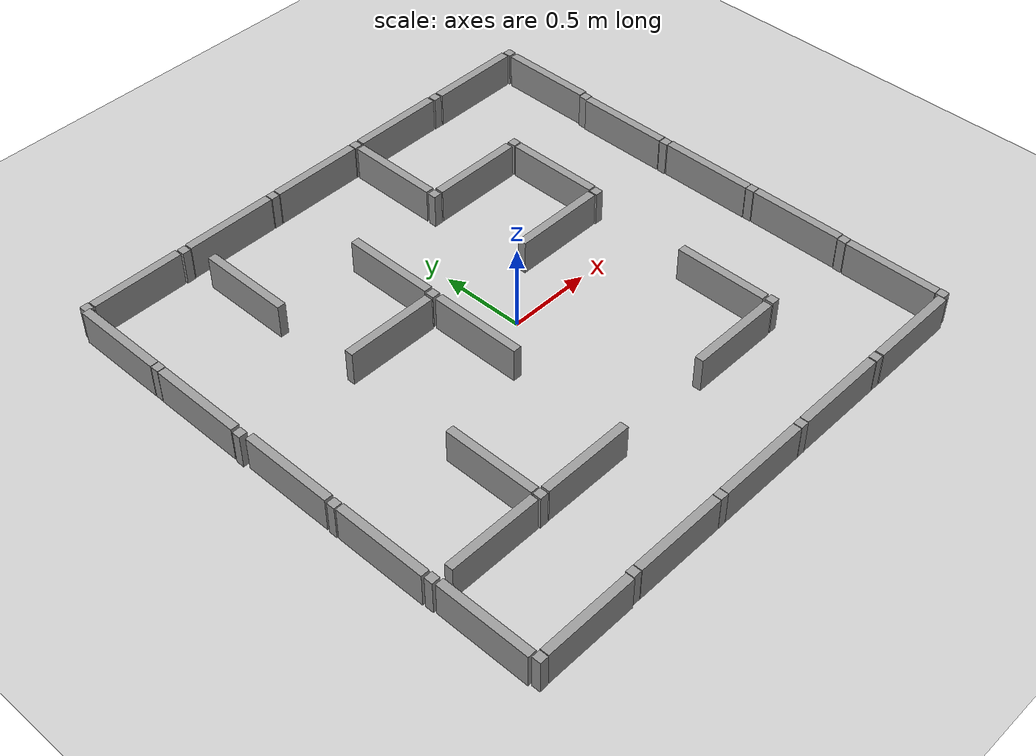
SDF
<?xml version="1.0" ?>

<sdf version='1.6'>
  <world name='default'>
    <light name='sun' type='directional'>
      <cast_shadows>1</cast_shadows>
      <pose frame=''>0 0 10 0 -0 0</pose>
      <diffuse>0.8 0.8 0.8 1</diffuse>
      <specular>0.2 0.2 0.2 1</specular>
      <attenuation>
        <range>1000</range>
        <constant>0.9</constant>
        <linear>0.01</linear>
        <quadratic>0.001</quadratic>
      </attenuation>
      <direction>-0.5 0.1 -0.9</direction>
    </light>
    <model name='ground_plane'>
      <static>1</static>
      <link name='link'>
        <collision name='collision'>
          <geometry>
            <plane>
              <normal>0 0 1</normal>
              <size>100 100</size>
            </plane>
          </geometry>
          <surface>
            <contact>
              <collide_bitmask>65535</collide_bitmask>
              <ode/>
            </contact>
            <friction>
              <ode>
                <mu>100</mu>
                <mu2>50</mu2>
              </ode>
              <torsional>
                <ode/>
              </torsional>
            </friction>
            <bounce/>
          </surface>
          <max_contacts>10</max_contacts>
        </collision>
        <visual name='visual'>
          <cast_shadows>0</cast_shadows>
          <geometry>
            <plane>
              <normal>0 0 1</normal>
              <size>100 100</size>
            </plane>
          </geometry>
          <material>
            <script>
              <uri>file://media/materials/scripts/gazebo.material</uri>
              <name>Gazebo/Grey</name>
            </script>
          </material>
        </visual>
        <self_collide>0</self_collide>
        <enable_wind>0</enable_wind>
        <kinematic>0</kinematic>
      </link>
    </model>
    <gravity>0 0 -9.8</gravity>
    <magnetic_field>6e-06 2.3e-05 -4.2e-05</magnetic_field>
    <atmosphere type='adiabatic'/>
    <physics name='default_physics' default='0' type='ode'>
      <max_step_size>0.001</max_step_size>
      <real_time_factor>1</real_time_factor>
      <real_time_update_rate>1000</real_time_update_rate>
    </physics>
    <scene>
      <ambient>0.4 0.4 0.4 1</ambient>
      <background>0.7 0.7 0.7 1</background>
      <shadows>1</shadows>
    </scene>
    <audio>
      <device>default</device>
    </audio>
    <wind/>
    <spherical_coordinates>
      <surface_model>EARTH_WGS84</surface_model>
      <latitude_deg>0</latitude_deg>
      <longitude_deg>0</longitude_deg>
      <elevation>0</elevation>
      <heading_deg>0</heading_deg>
    </spherical_coordinates>
      <model name='white_maze'>
        <link name='link_0'>
          <inertial>
            <mass>1</mass>
            <inertia>
              <ixx>0.166667</ixx>
              <ixy>0</ixy>
              <ixz>0</ixz>
              <iyy>0.166667</iyy>
              <iyz>0</iyz>
              <izz>0.166667</izz>
            </inertia>
            <pose frame=''>0 0 0 0 -0 0</pose>
          </inertial>
          <pose frame=''>-1.23382 -1.58127 0 0 -0 0</pose>
          <gravity>1</gravity>
          <self_collide>0</self_collide>
          <kinematic>0</kinematic>
          <enable_wind>0</enable_wind>
          <visual name='visual'>
            <pose frame=''>0 0 0 0 -0 0</pose>
            <geometry>
              <box>
                <size>0.55 0.05 0.4</size>
              </box>
            </geometry>
            <material>
              <lighting>1</lighting>
              <script>
                <uri>file://media/materials/scripts/gazebo.material</uri>
                <name>Gazebo/Grey</name>
              </script>
              <shader type='vertex'>
                <normal_map>__default__</normal_map>
              </shader>
              <ambient>1 1 1 1</ambient>
              <diffuse>0.7 0.7 0.7 1</diffuse>
              <specular>0.01 0.01 0.01 1</specular>
              <emissive>0 0 0 1</emissive>
            </material>
            <transparency>0</transparency>
            <cast_shadows>1</cast_shadows>
          </visual>
          <collision name='collision'>
            <laser_retro>0</laser_retro>
            <max_contacts>10</max_contacts>
            <pose frame=''>0 0 0 0 -0 0</pose>
            <geometry>
              <box>
                <size>0.55 0.05 0.4</size>
              </box>
            </geometry>
            <surface>
              <friction>
                <ode>
                  <mu>1</mu>
                  <mu2>1</mu2>
                  <fdir1>0 0 0</fdir1>
                  <slip1>0</slip1>
                  <slip2>0</slip2>
                </ode>
                <torsional>
                  <coefficient>1</coefficient>
                  <patch_radius>0</patch_radius>
                  <surface_radius>0</surface_radius>
                  <use_patch_radius>1</use_patch_radius>
                  <ode>
                    <slip>0</slip>
                  </ode>
                </torsional>
              </friction>
              <bounce>
                <restitution_coefficient>0</restitution_coefficient>
                <threshold>1e+06</threshold>
              </bounce>
              <contact>
                <collide_without_contact>0</collide_without_contact>
                <collide_without_contact_bitmask>1</collide_without_contact_bitmask>
                <collide_bitmask>1</collide_bitmask>
                <ode>
                  <soft_cfm>0</soft_cfm>
                  <soft_erp>0.2</soft_erp>
                  <kp>1e+13</kp>
                  <kd>1</kd>
                  <max_vel>0.01</max_vel>
                  <min_depth>0</min_depth>
                </ode>
                <bullet>
                  <split_impulse>1</split_impulse>
                  <split_impulse_penetration_threshold>-0.01</split_impulse_penetration_threshold>
                  <soft_cfm>0</soft_cfm>
                  <soft_erp>0.2</soft_erp>
                  <kp>1e+13</kp>
                  <kd>1</kd>
                </bullet>
              </contact>
            </surface>
          </collision>
        </link>
        <link name='link_0_clone'>
          <inertial>
            <mass>1</mass>
            <inertia>
              <ixx>0.166667</ixx>
              <ixy>0</ixy>
              <ixz>0</ixz>
              <iyy>0.166667</iyy>
              <iyz>0</iyz>
              <izz>0.166667</izz>
            </inertia>
            <pose frame=''>0 0 0 0 -0 0</pose>
          </inertial>
          <pose frame=''>-0.627493 -1.57445 0 0 -0 0</pose>
          <gravity>1</gravity>
          <self_collide>0</self_collide>
          <kinematic>0</kinematic>
          <enable_wind>0</enable_wind>
          <visual name='visual'>
            <pose frame=''>0 0 0 0 -0 0</pose>
            <geometry>
              <box>
                <size>0.55 0.05 0.4</size>
              </box>
            </geometry>
            <material>
              <lighting>1</lighting>
              <script>
                <uri>file://media/materials/scripts/gazebo.material</uri>
                <name>Gazebo/Grey</name>
              </script>
              <shader type='vertex'>
                <normal_map>__default__</normal_map>
              </shader>
              <ambient>1 1 1 1</ambient>
              <diffuse>0.7 0.7 0.7 1</diffuse>
              <specular>0.01 0.01 0.01 1</specular>
              <emissive>0 0 0 1</emissive>
            </material>
            <transparency>0</transparency>
            <cast_shadows>1</cast_shadows>
          </visual>
          <collision name='collision'>
            <laser_retro>0</laser_retro>
            <max_contacts>10</max_contacts>
            <pose frame=''>0 0 0 0 -0 0</pose>
            <geometry>
              <box>
                <size>0.55 0.05 0.4</size>
              </box>
            </geometry>
            <surface>
              <friction>
                <ode>
                  <mu>1</mu>
                  <mu2>1</mu2>
                  <fdir1>0 0 0</fdir1>
                  <slip1>0</slip1>
                  <slip2>0</slip2>
                </ode>
                <torsional>
                  <coefficient>1</coefficient>
                  <patch_radius>0</patch_radius>
                  <surface_radius>0</surface_radius>
                  <use_patch_radius>1</use_patch_radius>
                  <ode>
                    <slip>0</slip>
                  </ode>
                </torsional>
              </friction>
              <bounce>
                <restitution_coefficient>0</restitution_coefficient>
                <threshold>1e+06</threshold>
              </bounce>
              <contact>
                <collide_without_contact>0</collide_without_contact>
                <collide_without_contact_bitmask>1</collide_without_contact_bitmask>
                <collide_bitmask>1</collide_bitmask>
                <ode>
                  <soft_cfm>0</soft_cfm>
                  <soft_erp>0.2</soft_erp>
                  <kp>1e+13</kp>
                  <kd>1</kd>
                  <max_vel>0.01</max_vel>
                  <min_depth>0</min_depth>
                </ode>
                <bullet>
                  <split_impulse>1</split_impulse>
                  <split_impulse_penetration_threshold>-0.01</split_impulse_penetration_threshold>
                  <soft_cfm>0</soft_cfm>
                  <soft_erp>0.2</soft_erp>
                  <kp>1e+13</kp>
                  <kd>1</kd>
                </bullet>
              </contact>
            </surface>
          </collision>
        </link>
        <link name='link_0_clone_0'>
          <inertial>
            <mass>1</mass>
            <inertia>
              <ixx>0.166667</ixx>
              <ixy>0</ixy>
              <ixz>0</ixz>
              <iyy>0.166667</iyy>
              <iyz>0</iyz>
              <izz>0.166667</izz>
            </inertia>
            <pose frame=''>0 0 0 0 -0 0</pose>
          </inertial>
          <pose frame=''>-0.023747 -1.57344 0 0 -0 0</pose>
          <gravity>1</gravity>
          <self_collide>0</self_collide>
          <kinematic>0</kinematic>
          <enable_wind>0</enable_wind>
          <visual name='visual'>
            <pose frame=''>0 0 0 0 -0 0</pose>
            <geometry>
              <box>
                <size>0.55 0.05 0.4</size>
              </box>
            </geometry>
            <material>
              <lighting>1</lighting>
              <script>
                <uri>file://media/materials/scripts/gazebo.material</uri>
                <name>Gazebo/Grey</name>
              </script>
              <shader type='vertex'>
                <normal_map>__default__</normal_map>
              </shader>
              <ambient>1 1 1 1</ambient>
              <diffuse>0.7 0.7 0.7 1</diffuse>
              <specular>0.01 0.01 0.01 1</specular>
              <emissive>0 0 0 1</emissive>
            </material>
            <transparency>0</transparency>
            <cast_shadows>1</cast_shadows>
          </visual>
          <collision name='collision'>
            <laser_retro>0</laser_retro>
            <max_contacts>10</max_contacts>
            <pose frame=''>0 0 0 0 -0 0</pose>
            <geometry>
              <box>
                <size>0.55 0.05 0.4</size>
              </box>
            </geometry>
            <surface>
              <friction>
                <ode>
                  <mu>1</mu>
                  <mu2>1</mu2>
                  <fdir1>0 0 0</fdir1>
                  <slip1>0</slip1>
                  <slip2>0</slip2>
                </ode>
                <torsional>
                  <coefficient>1</coefficient>
                  <patch_radius>0</patch_radius>
                  <surface_radius>0</surface_radius>
                  <use_patch_radius>1</use_patch_radius>
                  <ode>
                    <slip>0</slip>
                  </ode>
                </torsional>
              </friction>
              <bounce>
                <restitution_coefficient>0</restitution_coefficient>
                <threshold>1e+06</threshold>
              </bounce>
              <contact>
                <collide_without_contact>0</collide_without_contact>
                <collide_without_contact_bitmask>1</collide_without_contact_bitmask>
                <collide_bitmask>1</collide_bitmask>
                <ode>
                  <soft_cfm>0</soft_cfm>
                  <soft_erp>0.2</soft_erp>
                  <kp>1e+13</kp>
                  <kd>1</kd>
                  <max_vel>0.01</max_vel>
                  <min_depth>0</min_depth>
                </ode>
                <bullet>
                  <split_impulse>1</split_impulse>
                  <split_impulse_penetration_threshold>-0.01</split_impulse_penetration_threshold>
                  <soft_cfm>0</soft_cfm>
                  <soft_erp>0.2</soft_erp>
                  <kp>1e+13</kp>
                  <kd>1</kd>
                </bullet>
              </contact>
            </surface>
          </collision>
        </link>
        <link name='link_0_clone_1'>
          <inertial>
            <mass>1</mass>
            <inertia>
              <ixx>0.166667</ixx>
              <ixy>0</ixy>
              <ixz>0</ixz>
              <iyy>0.166667</iyy>
              <iyz>0</iyz>
              <izz>0.166667</izz>
            </inertia>
            <pose frame=''>0 0 0 0 -0 0</pose>
          </inertial>
          <pose frame=''>0.582587 -1.57153 0 0 -0 0</pose>
          <gravity>1</gravity>
          <self_collide>0</self_collide>
          <kinematic>0</kinematic>
          <enable_wind>0</enable_wind>
          <visual name='visual'>
            <pose frame=''>0 0 0 0 -0 0</pose>
            <geometry>
              <box>
                <size>0.55 0.05 0.4</size>
              </box>
            </geometry>
            <material>
              <lighting>1</lighting>
              <script>
                <uri>file://media/materials/scripts/gazebo.material</uri>
                <name>Gazebo/Grey</name>
              </script>
              <shader type='vertex'>
                <normal_map>__default__</normal_map>
              </shader>
              <ambient>1 1 1 1</ambient>
              <diffuse>0.7 0.7 0.7 1</diffuse>
              <specular>0.01 0.01 0.01 1</specular>
              <emissive>0 0 0 1</emissive>
            </material>
            <transparency>0</transparency>
            <cast_shadows>1</cast_shadows>
          </visual>
          <collision name='collision'>
            <laser_retro>0</laser_retro>
            <max_contacts>10</max_contacts>
            <pose frame=''>0 0 0 0 -0 0</pose>
            <geometry>
              <box>
                <size>0.55 0.05 0.4</size>
              </box>
            </geometry>
            <surface>
              <friction>
                <ode>
                  <mu>1</mu>
                  <mu2>1</mu2>
                  <fdir1>0 0 0</fdir1>
                  <slip1>0</slip1>
                  <slip2>0</slip2>
                </ode>
                <torsional>
                  <coefficient>1</coefficient>
                  <patch_radius>0</patch_radius>
                  <surface_radius>0</surface_radius>
                  <use_patch_radius>1</use_patch_radius>
                  <ode>
                    <slip>0</slip>
                  </ode>
                </torsional>
              </friction>
              <bounce>
                <restitution_coefficient>0</restitution_coefficient>
                <threshold>1e+06</threshold>
              </bounce>
              <contact>
                <collide_without_contact>0</collide_without_contact>
                <collide_without_contact_bitmask>1</collide_without_contact_bitmask>
                <collide_bitmask>1</collide_bitmask>
                <ode>
                  <soft_cfm>0</soft_cfm>
                  <soft_erp>0.2</soft_erp>
                  <kp>1e+13</kp>
                  <kd>1</kd>
                  <max_vel>0.01</max_vel>
                  <min_depth>0</min_depth>
                </ode>
                <bullet>
                  <split_impulse>1</split_impulse>
                  <split_impulse_penetration_threshold>-0.01</split_impulse_penetration_threshold>
                  <soft_cfm>0</soft_cfm>
                  <soft_erp>0.2</soft_erp>
                  <kp>1e+13</kp>
                  <kd>1</kd>
                </bullet>
              </contact>
            </surface>
          </collision>
        </link>
        <link name='link_0_clone_1_clone'>
          <inertial>
            <mass>1</mass>
            <inertia>
              <ixx>0.166667</ixx>
              <ixy>0</ixy>
              <ixz>0</ixz>
              <iyy>0.166667</iyy>
              <iyz>0</iyz>
              <izz>0.166667</izz>
            </inertia>
            <pose frame=''>0 0 0 0 -0 0</pose>
          </inertial>
          <pose frame=''>1.49724 -1.25172 0 0 0 -1.57264</pose>
          <gravity>1</gravity>
          <self_collide>0</self_collide>
          <kinematic>0</kinematic>
          <enable_wind>0</enable_wind>
          <visual name='visual'>
            <pose frame=''>0 0 0 0 -0 0</pose>
            <geometry>
              <box>
                <size>0.55 0.05 0.4</size>
              </box>
            </geometry>
            <material>
              <lighting>1</lighting>
              <script>
                <uri>file://media/materials/scripts/gazebo.material</uri>
                <name>Gazebo/Grey</name>
              </script>
              <shader type='vertex'>
                <normal_map>__default__</normal_map>
              </shader>
              <ambient>1 1 1 1</ambient>
              <diffuse>0.7 0.7 0.7 1</diffuse>
              <specular>0.01 0.01 0.01 1</specular>
              <emissive>0 0 0 1</emissive>
            </material>
            <transparency>0</transparency>
            <cast_shadows>1</cast_shadows>
          </visual>
          <collision name='collision'>
            <laser_retro>0</laser_retro>
            <max_contacts>10</max_contacts>
            <pose frame=''>0 0 0 0 -0 0</pose>
            <geometry>
              <box>
                <size>0.55 0.05 0.4</size>
              </box>
            </geometry>
            <surface>
              <friction>
                <ode>
                  <mu>1</mu>
                  <mu2>1</mu2>
                  <fdir1>0 0 0</fdir1>
                  <slip1>0</slip1>
                  <slip2>0</slip2>
                </ode>
                <torsional>
                  <coefficient>1</coefficient>
                  <patch_radius>0</patch_radius>
                  <surface_radius>0</surface_radius>
                  <use_patch_radius>1</use_patch_radius>
                  <ode>
                    <slip>0</slip>
                  </ode>
                </torsional>
              </friction>
              <bounce>
                <restitution_coefficient>0</restitution_coefficient>
                <threshold>1e+06</threshold>
              </bounce>
              <contact>
                <collide_without_contact>0</collide_without_contact>
                <collide_without_contact_bitmask>1</collide_without_contact_bitmask>
                <collide_bitmask>1</collide_bitmask>
                <ode>
                  <soft_cfm>0</soft_cfm>
                  <soft_erp>0.2</soft_erp>
                  <kp>1e+13</kp>
                  <kd>1</kd>
                  <max_vel>0.01</max_vel>
                  <min_depth>0</min_depth>
                </ode>
                <bullet>
                  <split_impulse>1</split_impulse>
                  <split_impulse_penetration_threshold>-0.01</split_impulse_penetration_threshold>
                  <soft_cfm>0</soft_cfm>
                  <soft_erp>0.2</soft_erp>
                  <kp>1e+13</kp>
                  <kd>1</kd>
                </bullet>
              </contact>
            </surface>
          </collision>
        </link>
        <link name='link_0_clone_1_clone_0'>
          <inertial>
            <mass>1</mass>
            <inertia>
              <ixx>0.166667</ixx>
              <ixy>0</ixy>
              <ixz>0</ixz>
              <iyy>0.166667</iyy>
              <iyz>0</iyz>
              <izz>0.166667</izz>
            </inertia>
            <pose frame=''>0 0 0 0 -0 0</pose>
          </inertial>
          <pose frame=''>1.21099 1.50565 0 0 -0 0</pose>
          <gravity>1</gravity>
          <self_collide>0</self_collide>
          <kinematic>0</kinematic>
          <enable_wind>0</enable_wind>
          <visual name='visual'>
            <pose frame=''>0 0 0 0 -0 0</pose>
            <geometry>
              <box>
                <size>0.55 0.05 0.4</size>
              </box>
            </geometry>
            <material>
              <lighting>1</lighting>
              <script>
                <uri>file://media/materials/scripts/gazebo.material</uri>
                <name>Gazebo/Grey</name>
              </script>
              <shader type='vertex'>
                <normal_map>__default__</normal_map>
              </shader>
              <ambient>1 1 1 1</ambient>
              <diffuse>0.7 0.7 0.7 1</diffuse>
              <specular>0.01 0.01 0.01 1</specular>
              <emissive>0 0 0 1</emissive>
            </material>
            <transparency>0</transparency>
            <cast_shadows>1</cast_shadows>
          </visual>
          <collision name='collision'>
            <laser_retro>0</laser_retro>
            <max_contacts>10</max_contacts>
            <pose frame=''>0 0 0 0 -0 0</pose>
            <geometry>
              <box>
                <size>0.55 0.05 0.4</size>
              </box>
            </geometry>
            <surface>
              <friction>
                <ode>
                  <mu>1</mu>
                  <mu2>1</mu2>
                  <fdir1>0 0 0</fdir1>
                  <slip1>0</slip1>
                  <slip2>0</slip2>
                </ode>
                <torsional>
                  <coefficient>1</coefficient>
                  <patch_radius>0</patch_radius>
                  <surface_radius>0</surface_radius>
                  <use_patch_radius>1</use_patch_radius>
                  <ode>
                    <slip>0</slip>
                  </ode>
                </torsional>
              </friction>
              <bounce>
                <restitution_coefficient>0</restitution_coefficient>
                <threshold>1e+06</threshold>
              </bounce>
              <contact>
                <collide_without_contact>0</collide_without_contact>
                <collide_without_contact_bitmask>1</collide_without_contact_bitmask>
                <collide_bitmask>1</collide_bitmask>
                <ode>
                  <soft_cfm>0</soft_cfm>
                  <soft_erp>0.2</soft_erp>
                  <kp>1e+13</kp>
                  <kd>1</kd>
                  <max_vel>0.01</max_vel>
                  <min_depth>0</min_depth>
                </ode>
                <bullet>
                  <split_impulse>1</split_impulse>
                  <split_impulse_penetration_threshold>-0.01</split_impulse_penetration_threshold>
                  <soft_cfm>0</soft_cfm>
                  <soft_erp>0.2</soft_erp>
                  <kp>1e+13</kp>
                  <kd>1</kd>
                </bullet>
              </contact>
            </surface>
          </collision>
        </link>
        <link name='link_0_clone_1_clone_1'>
          <inertial>
            <mass>1</mass>
            <inertia>
              <ixx>0.166667</ixx>
              <ixy>0</ixy>
              <ixz>0</ixz>
              <iyy>0.166667</iyy>
              <iyz>0</iyz>
              <izz>0.166667</izz>
            </inertia>
            <pose frame=''>0 0 0 0 -0 0</pose>
          </inertial>
          <pose frame=''>0.593667 1.50999 0 0 -0 0</pose>
          <gravity>1</gravity>
          <self_collide>0</self_collide>
          <kinematic>0</kinematic>
          <enable_wind>0</enable_wind>
          <visual name='visual'>
            <pose frame=''>0 0 0 0 -0 0</pose>
            <geometry>
              <box>
                <size>0.55 0.05 0.4</size>
              </box>
            </geometry>
            <material>
              <lighting>1</lighting>
              <script>
                <uri>file://media/materials/scripts/gazebo.material</uri>
                <name>Gazebo/Grey</name>
              </script>
              <shader type='vertex'>
                <normal_map>__default__</normal_map>
              </shader>
              <ambient>1 1 1 1</ambient>
              <diffuse>0.7 0.7 0.7 1</diffuse>
              <specular>0.01 0.01 0.01 1</specular>
              <emissive>0 0 0 1</emissive>
            </material>
            <transparency>0</transparency>
            <cast_shadows>1</cast_shadows>
          </visual>
          <collision name='collision'>
            <laser_retro>0</laser_retro>
            <max_contacts>10</max_contacts>
            <pose frame=''>0 0 0 0 -0 0</pose>
            <geometry>
              <box>
                <size>0.55 0.05 0.4</size>
              </box>
            </geometry>
            <surface>
              <friction>
                <ode>
                  <mu>1</mu>
                  <mu2>1</mu2>
                  <fdir1>0 0 0</fdir1>
                  <slip1>0</slip1>
                  <slip2>0</slip2>
                </ode>
                <torsional>
                  <coefficient>1</coefficient>
                  <patch_radius>0</patch_radius>
                  <surface_radius>0</surface_radius>
                  <use_patch_radius>1</use_patch_radius>
                  <ode>
                    <slip>0</slip>
                  </ode>
                </torsional>
              </friction>
              <bounce>
                <restitution_coefficient>0</restitution_coefficient>
                <threshold>1e+06</threshold>
              </bounce>
              <contact>
                <collide_without_contact>0</collide_without_contact>
                <collide_without_contact_bitmask>1</collide_without_contact_bitmask>
                <collide_bitmask>1</collide_bitmask>
                <ode>
                  <soft_cfm>0</soft_cfm>
                  <soft_erp>0.2</soft_erp>
                  <kp>1e+13</kp>
                  <kd>1</kd>
                  <max_vel>0.01</max_vel>
                  <min_depth>0</min_depth>
                </ode>
                <bullet>
                  <split_impulse>1</split_impulse>
                  <split_impulse_penetration_threshold>-0.01</split_impulse_penetration_threshold>
                  <soft_cfm>0</soft_cfm>
                  <soft_erp>0.2</soft_erp>
                  <kp>1e+13</kp>
                  <kd>1</kd>
                </bullet>
              </contact>
            </surface>
          </collision>
        </link>
        <link name='link_0_clone_1_clone_2'>
          <inertial>
            <mass>1</mass>
            <inertia>
              <ixx>0.166667</ixx>
              <ixy>0</ixy>
              <ixz>0</ixz>
              <iyy>0.166667</iyy>
              <iyz>0</iyz>
              <izz>0.166667</izz>
            </inertia>
            <pose frame=''>0 0 0 0 -0 0</pose>
          </inertial>
          <pose frame=''>-0.019419 1.51088 0 0 -0 0</pose>
          <gravity>1</gravity>
          <self_collide>0</self_collide>
          <kinematic>0</kinematic>
          <enable_wind>0</enable_wind>
          <visual name='visual'>
            <pose frame=''>0 0 0 0 -0 0</pose>
            <geometry>
              <box>
                <size>0.55 0.05 0.4</size>
              </box>
            </geometry>
            <material>
              <lighting>1</lighting>
              <script>
                <uri>file://media/materials/scripts/gazebo.material</uri>
                <name>Gazebo/Grey</name>
              </script>
              <shader type='vertex'>
                <normal_map>__default__</normal_map>
              </shader>
              <ambient>1 1 1 1</ambient>
              <diffuse>0.7 0.7 0.7 1</diffuse>
              <specular>0.01 0.01 0.01 1</specular>
              <emissive>0 0 0 1</emissive>
            </material>
            <transparency>0</transparency>
            <cast_shadows>1</cast_shadows>
          </visual>
          <collision name='collision'>
            <laser_retro>0</laser_retro>
            <max_contacts>10</max_contacts>
            <pose frame=''>0 0 0 0 -0 0</pose>
            <geometry>
              <box>
                <size>0.55 0.05 0.4</size>
              </box>
            </geometry>
            <surface>
              <friction>
                <ode>
                  <mu>1</mu>
                  <mu2>1</mu2>
                  <fdir1>0 0 0</fdir1>
                  <slip1>0</slip1>
                  <slip2>0</slip2>
                </ode>
                <torsional>
                  <coefficient>1</coefficient>
                  <patch_radius>0</patch_radius>
                  <surface_radius>0</surface_radius>
                  <use_patch_radius>1</use_patch_radius>
                  <ode>
                    <slip>0</slip>
                  </ode>
                </torsional>
              </friction>
              <bounce>
                <restitution_coefficient>0</restitution_coefficient>
                <threshold>1e+06</threshold>
              </bounce>
              <contact>
                <collide_without_contact>0</collide_without_contact>
                <collide_without_contact_bitmask>1</collide_without_contact_bitmask>
                <collide_bitmask>1</collide_bitmask>
                <ode>
                  <soft_cfm>0</soft_cfm>
                  <soft_erp>0.2</soft_erp>
                  <kp>1e+13</kp>
                  <kd>1</kd>
                  <max_vel>0.01</max_vel>
                  <min_depth>0</min_depth>
                </ode>
                <bullet>
                  <split_impulse>1</split_impulse>
                  <split_impulse_penetration_threshold>-0.01</split_impulse_penetration_threshold>
                  <soft_cfm>0</soft_cfm>
                  <soft_erp>0.2</soft_erp>
                  <kp>1e+13</kp>
                  <kd>1</kd>
                </bullet>
              </contact>
            </surface>
          </collision>
        </link>
        <link name='link_0_clone_1_clone_3'>
          <inertial>
            <mass>1</mass>
            <inertia>
              <ixx>0.166667</ixx>
              <ixy>0</ixy>
              <ixz>0</ixz>
              <iyy>0.166667</iyy>
              <iyz>0</iyz>
              <izz>0.166667</izz>
            </inertia>
            <pose frame=''>0 0 0 0 -0 0</pose>
          </inertial>
          <pose frame=''>-0.630178 1.51122 0 0 -0 0</pose>
          <gravity>1</gravity>
          <self_collide>0</self_collide>
          <kinematic>0</kinematic>
          <enable_wind>0</enable_wind>
          <visual name='visual'>
            <pose frame=''>0 0 0 0 -0 0</pose>
            <geometry>
              <box>
                <size>0.55 0.05 0.4</size>
              </box>
            </geometry>
            <material>
              <lighting>1</lighting>
              <script>
                <uri>file://media/materials/scripts/gazebo.material</uri>
                <name>Gazebo/Grey</name>
              </script>
              <shader type='vertex'>
                <normal_map>__default__</normal_map>
              </shader>
              <ambient>1 1 1 1</ambient>
              <diffuse>0.7 0.7 0.7 1</diffuse>
              <specular>0.01 0.01 0.01 1</specular>
              <emissive>0 0 0 1</emissive>
            </material>
            <transparency>0</transparency>
            <cast_shadows>1</cast_shadows>
          </visual>
          <collision name='collision'>
            <laser_retro>0</laser_retro>
            <max_contacts>10</max_contacts>
            <pose frame=''>0 0 0 0 -0 0</pose>
            <geometry>
              <box>
                <size>0.55 0.05 0.4</size>
              </box>
            </geometry>
            <surface>
              <friction>
                <ode>
                  <mu>1</mu>
                  <mu2>1</mu2>
                  <fdir1>0 0 0</fdir1>
                  <slip1>0</slip1>
                  <slip2>0</slip2>
                </ode>
                <torsional>
                  <coefficient>1</coefficient>
                  <patch_radius>0</patch_radius>
                  <surface_radius>0</surface_radius>
                  <use_patch_radius>1</use_patch_radius>
                  <ode>
                    <slip>0</slip>
                  </ode>
                </torsional>
              </friction>
              <bounce>
                <restitution_coefficient>0</restitution_coefficient>
                <threshold>1e+06</threshold>
              </bounce>
              <contact>
                <collide_without_contact>0</collide_without_contact>
                <collide_without_contact_bitmask>1</collide_without_contact_bitmask>
                <collide_bitmask>1</collide_bitmask>
                <ode>
                  <soft_cfm>0</soft_cfm>
                  <soft_erp>0.2</soft_erp>
                  <kp>1e+13</kp>
                  <kd>1</kd>
                  <max_vel>0.01</max_vel>
                  <min_depth>0</min_depth>
                </ode>
                <bullet>
                  <split_impulse>1</split_impulse>
                  <split_impulse_penetration_threshold>-0.01</split_impulse_penetration_threshold>
                  <soft_cfm>0</soft_cfm>
                  <soft_erp>0.2</soft_erp>
                  <kp>1e+13</kp>
                  <kd>1</kd>
                </bullet>
              </contact>
            </surface>
          </collision>
        </link>
        <link name='link_0_clone_1_clone_4'>
          <inertial>
            <mass>1</mass>
            <inertia>
              <ixx>0.166667</ixx>
              <ixy>0</ixy>
              <ixz>0</ixz>
              <iyy>0.166667</iyy>
              <iyz>0</iyz>
              <izz>0.166667</izz>
            </inertia>
            <pose frame=''>0 0 0 0 -0 0</pose>
          </inertial>
          <pose frame=''>-1.24431 1.51418 0 0 -0 0</pose>
          <gravity>1</gravity>
          <self_collide>0</self_collide>
          <kinematic>0</kinematic>
          <enable_wind>0</enable_wind>
          <visual name='visual'>
            <pose frame=''>0 0 0 0 -0 0</pose>
            <geometry>
              <box>
                <size>0.55 0.05 0.4</size>
              </box>
            </geometry>
            <material>
              <lighting>1</lighting>
              <script>
                <uri>file://media/materials/scripts/gazebo.material</uri>
                <name>Gazebo/Grey</name>
              </script>
              <shader type='vertex'>
                <normal_map>__default__</normal_map>
              </shader>
              <ambient>1 1 1 1</ambient>
              <diffuse>0.7 0.7 0.7 1</diffuse>
              <specular>0.01 0.01 0.01 1</specular>
              <emissive>0 0 0 1</emissive>
            </material>
            <transparency>0</transparency>
            <cast_shadows>1</cast_shadows>
          </visual>
          <collision name='collision'>
            <laser_retro>0</laser_retro>
            <max_contacts>10</max_contacts>
            <pose frame=''>0 0 0 0 -0 0</pose>
            <geometry>
              <box>
                <size>0.55 0.05 0.4</size>
              </box>
            </geometry>
            <surface>
              <friction>
                <ode>
                  <mu>1</mu>
                  <mu2>1</mu2>
                  <fdir1>0 0 0</fdir1>
                  <slip1>0</slip1>
                  <slip2>0</slip2>
                </ode>
                <torsional>
                  <coefficient>1</coefficient>
                  <patch_radius>0</patch_radius>
                  <surface_radius>0</surface_radius>
                  <use_patch_radius>1</use_patch_radius>
                  <ode>
                    <slip>0</slip>
                  </ode>
                </torsional>
              </friction>
              <bounce>
                <restitution_coefficient>0</restitution_coefficient>
                <threshold>1e+06</threshold>
              </bounce>
              <contact>
                <collide_without_contact>0</collide_without_contact>
                <collide_without_contact_bitmask>1</collide_without_contact_bitmask>
                <collide_bitmask>1</collide_bitmask>
                <ode>
                  <soft_cfm>0</soft_cfm>
                  <soft_erp>0.2</soft_erp>
                  <kp>1e+13</kp>
                  <kd>1</kd>
                  <max_vel>0.01</max_vel>
                  <min_depth>0</min_depth>
                </ode>
                <bullet>
                  <split_impulse>1</split_impulse>
                  <split_impulse_penetration_threshold>-0.01</split_impulse_penetration_threshold>
                  <soft_cfm>0</soft_cfm>
                  <soft_erp>0.2</soft_erp>
                  <kp>1e+13</kp>
                  <kd>1</kd>
                </bullet>
              </contact>
            </surface>
          </collision>
        </link>
        <link name='link_0_clone_1_clone_clone'>
          <inertial>
            <mass>1</mass>
            <inertia>
              <ixx>0.166667</ixx>
              <ixy>0</ixy>
              <ixz>0</ixz>
              <iyy>0.166667</iyy>
              <iyz>0</iyz>
              <izz>0.166667</izz>
            </inertia>
            <pose frame=''>0 0 0 0 -0 0</pose>
          </inertial>
          <pose frame=''>1.504 -0.640018 0 0 0 -1.57264</pose>
          <gravity>1</gravity>
          <self_collide>0</self_collide>
          <kinematic>0</kinematic>
          <enable_wind>0</enable_wind>
          <visual name='visual'>
            <pose frame=''>0 0 0 0 -0 0</pose>
            <geometry>
              <box>
                <size>0.55 0.05 0.4</size>
              </box>
            </geometry>
            <material>
              <lighting>1</lighting>
              <script>
                <uri>file://media/materials/scripts/gazebo.material</uri>
                <name>Gazebo/Grey</name>
              </script>
              <shader type='vertex'>
                <normal_map>__default__</normal_map>
              </shader>
              <ambient>1 1 1 1</ambient>
              <diffuse>0.7 0.7 0.7 1</diffuse>
              <specular>0.01 0.01 0.01 1</specular>
              <emissive>0 0 0 1</emissive>
            </material>
            <transparency>0</transparency>
            <cast_shadows>1</cast_shadows>
          </visual>
          <collision name='collision'>
            <laser_retro>0</laser_retro>
            <max_contacts>10</max_contacts>
            <pose frame=''>0 0 0 0 -0 0</pose>
            <geometry>
              <box>
                <size>0.55 0.05 0.4</size>
              </box>
            </geometry>
            <surface>
              <friction>
                <ode>
                  <mu>1</mu>
                  <mu2>1</mu2>
                  <fdir1>0 0 0</fdir1>
                  <slip1>0</slip1>
                  <slip2>0</slip2>
                </ode>
                <torsional>
                  <coefficient>1</coefficient>
                  <patch_radius>0</patch_radius>
                  <surface_radius>0</surface_radius>
                  <use_patch_radius>1</use_patch_radius>
                  <ode>
                    <slip>0</slip>
                  </ode>
                </torsional>
              </friction>
              <bounce>
                <restitution_coefficient>0</restitution_coefficient>
                <threshold>1e+06</threshold>
              </bounce>
              <contact>
                <collide_without_contact>0</collide_without_contact>
                <collide_without_contact_bitmask>1</collide_without_contact_bitmask>
                <collide_bitmask>1</collide_bitmask>
                <ode>
                  <soft_cfm>0</soft_cfm>
                  <soft_erp>0.2</soft_erp>
                  <kp>1e+13</kp>
                  <kd>1</kd>
                  <max_vel>0.01</max_vel>
                  <min_depth>0</min_depth>
                </ode>
                <bullet>
                  <split_impulse>1</split_impulse>
                  <split_impulse_penetration_threshold>-0.01</split_impulse_penetration_threshold>
                  <soft_cfm>0</soft_cfm>
                  <soft_erp>0.2</soft_erp>
                  <kp>1e+13</kp>
                  <kd>1</kd>
                </bullet>
              </contact>
            </surface>
          </collision>
        </link>
        <link name='link_0_clone_1_clone_clone_0'>
          <inertial>
            <mass>1</mass>
            <inertia>
              <ixx>0.166667</ixx>
              <ixy>0</ixy>
              <ixz>0</ixz>
              <iyy>0.166667</iyy>
              <iyz>0</iyz>
              <izz>0.166667</izz>
            </inertia>
            <pose frame=''>0 0 0 0 -0 0</pose>
          </inertial>
          <pose frame=''>1.50232 -0.033133 0 0 0 -1.57264</pose>
          <gravity>1</gravity>
          <self_collide>0</self_collide>
          <kinematic>0</kinematic>
          <enable_wind>0</enable_wind>
          <visual name='visual'>
            <pose frame=''>0 0 0 0 -0 0</pose>
            <geometry>
              <box>
                <size>0.55 0.05 0.4</size>
              </box>
            </geometry>
            <material>
              <lighting>1</lighting>
              <script>
                <uri>file://media/materials/scripts/gazebo.material</uri>
                <name>Gazebo/Grey</name>
              </script>
              <shader type='vertex'>
                <normal_map>__default__</normal_map>
              </shader>
              <ambient>1 1 1 1</ambient>
              <diffuse>0.7 0.7 0.7 1</diffuse>
              <specular>0.01 0.01 0.01 1</specular>
              <emissive>0 0 0 1</emissive>
            </material>
            <transparency>0</transparency>
            <cast_shadows>1</cast_shadows>
          </visual>
          <collision name='collision'>
            <laser_retro>0</laser_retro>
            <max_contacts>10</max_contacts>
            <pose frame=''>0 0 0 0 -0 0</pose>
            <geometry>
              <box>
                <size>0.55 0.05 0.4</size>
              </box>
            </geometry>
            <surface>
              <friction>
                <ode>
                  <mu>1</mu>
                  <mu2>1</mu2>
                  <fdir1>0 0 0</fdir1>
                  <slip1>0</slip1>
                  <slip2>0</slip2>
                </ode>
                <torsional>
                  <coefficient>1</coefficient>
                  <patch_radius>0</patch_radius>
                  <surface_radius>0</surface_radius>
                  <use_patch_radius>1</use_patch_radius>
                  <ode>
                    <slip>0</slip>
                  </ode>
                </torsional>
              </friction>
              <bounce>
                <restitution_coefficient>0</restitution_coefficient>
                <threshold>1e+06</threshold>
              </bounce>
              <contact>
                <collide_without_contact>0</collide_without_contact>
                <collide_without_contact_bitmask>1</collide_without_contact_bitmask>
                <collide_bitmask>1</collide_bitmask>
                <ode>
                  <soft_cfm>0</soft_cfm>
                  <soft_erp>0.2</soft_erp>
                  <kp>1e+13</kp>
                  <kd>1</kd>
                  <max_vel>0.01</max_vel>
                  <min_depth>0</min_depth>
                </ode>
                <bullet>
                  <split_impulse>1</split_impulse>
                  <split_impulse_penetration_threshold>-0.01</split_impulse_penetration_threshold>
                  <soft_cfm>0</soft_cfm>
                  <soft_erp>0.2</soft_erp>
                  <kp>1e+13</kp>
                  <kd>1</kd>
                </bullet>
              </contact>
            </surface>
          </collision>
        </link>
        <link name='link_0_clone_1_clone_clone_1'>
          <inertial>
            <mass>1</mass>
            <inertia>
              <ixx>0.166667</ixx>
              <ixy>0</ixy>
              <ixz>0</ixz>
              <iyy>0.166667</iyy>
              <iyz>0</iyz>
              <izz>0.166667</izz>
            </inertia>
            <pose frame=''>0 0 0 0 -0 0</pose>
          </inertial>
          <pose frame=''>1.49955 0.57556 0 0 0 -1.57264</pose>
          <gravity>1</gravity>
          <self_collide>0</self_collide>
          <kinematic>0</kinematic>
          <enable_wind>0</enable_wind>
          <visual name='visual'>
            <pose frame=''>0 0 0 0 -0 0</pose>
            <geometry>
              <box>
                <size>0.55 0.05 0.4</size>
              </box>
            </geometry>
            <material>
              <lighting>1</lighting>
              <script>
                <uri>file://media/materials/scripts/gazebo.material</uri>
                <name>Gazebo/Grey</name>
              </script>
              <shader type='vertex'>
                <normal_map>__default__</normal_map>
              </shader>
              <ambient>1 1 1 1</ambient>
              <diffuse>0.7 0.7 0.7 1</diffuse>
              <specular>0.01 0.01 0.01 1</specular>
              <emissive>0 0 0 1</emissive>
            </material>
            <transparency>0</transparency>
            <cast_shadows>1</cast_shadows>
          </visual>
          <collision name='collision'>
            <laser_retro>0</laser_retro>
            <max_contacts>10</max_contacts>
            <pose frame=''>0 0 0 0 -0 0</pose>
            <geometry>
              <box>
                <size>0.55 0.05 0.4</size>
              </box>
            </geometry>
            <surface>
              <friction>
                <ode>
                  <mu>1</mu>
                  <mu2>1</mu2>
                  <fdir1>0 0 0</fdir1>
                  <slip1>0</slip1>
                  <slip2>0</slip2>
                </ode>
                <torsional>
                  <coefficient>1</coefficient>
                  <patch_radius>0</patch_radius>
                  <surface_radius>0</surface_radius>
                  <use_patch_radius>1</use_patch_radius>
                  <ode>
                    <slip>0</slip>
                  </ode>
                </torsional>
              </friction>
              <bounce>
                <restitution_coefficient>0</restitution_coefficient>
                <threshold>1e+06</threshold>
              </bounce>
              <contact>
                <collide_without_contact>0</collide_without_contact>
                <collide_without_contact_bitmask>1</collide_without_contact_bitmask>
                <collide_bitmask>1</collide_bitmask>
                <ode>
                  <soft_cfm>0</soft_cfm>
                  <soft_erp>0.2</soft_erp>
                  <kp>1e+13</kp>
                  <kd>1</kd>
                  <max_vel>0.01</max_vel>
                  <min_depth>0</min_depth>
                </ode>
                <bullet>
                  <split_impulse>1</split_impulse>
                  <split_impulse_penetration_threshold>-0.01</split_impulse_penetration_threshold>
                  <soft_cfm>0</soft_cfm>
                  <soft_erp>0.2</soft_erp>
                  <kp>1e+13</kp>
                  <kd>1</kd>
                </bullet>
              </contact>
            </surface>
          </collision>
        </link>
        <link name='link_0_clone_1_clone_clone_1_clone'>
          <inertial>
            <mass>1</mass>
            <inertia>
              <ixx>0.166667</ixx>
              <ixy>0</ixy>
              <ixz>0</ixz>
              <iyy>0.166667</iyy>
              <iyz>0</iyz>
              <izz>0.166667</izz>
            </inertia>
            <pose frame=''>0 0 0 0 -0 0</pose>
          </inertial>
          <pose frame=''>-1.54904 -1.27572 0 0 0 -1.57264</pose>
          <gravity>1</gravity>
          <self_collide>0</self_collide>
          <kinematic>0</kinematic>
          <enable_wind>0</enable_wind>
          <visual name='visual'>
            <pose frame=''>0 0 0 0 -0 0</pose>
            <geometry>
              <box>
                <size>0.55 0.05 0.4</size>
              </box>
            </geometry>
            <material>
              <lighting>1</lighting>
              <script>
                <uri>file://media/materials/scripts/gazebo.material</uri>
                <name>Gazebo/Grey</name>
              </script>
              <shader type='vertex'>
                <normal_map>__default__</normal_map>
              </shader>
              <ambient>1 1 1 1</ambient>
              <diffuse>0.7 0.7 0.7 1</diffuse>
              <specular>0.01 0.01 0.01 1</specular>
              <emissive>0 0 0 1</emissive>
            </material>
            <transparency>0</transparency>
            <cast_shadows>1</cast_shadows>
          </visual>
          <collision name='collision'>
            <laser_retro>0</laser_retro>
            <max_contacts>10</max_contacts>
            <pose frame=''>0 0 0 0 -0 0</pose>
            <geometry>
              <box>
                <size>0.55 0.05 0.4</size>
              </box>
            </geometry>
            <surface>
              <friction>
                <ode>
                  <mu>1</mu>
                  <mu2>1</mu2>
                  <fdir1>0 0 0</fdir1>
                  <slip1>0</slip1>
                  <slip2>0</slip2>
                </ode>
                <torsional>
                  <coefficient>1</coefficient>
                  <patch_radius>0</patch_radius>
                  <surface_radius>0</surface_radius>
                  <use_patch_radius>1</use_patch_radius>
                  <ode>
                    <slip>0</slip>
                  </ode>
                </torsional>
              </friction>
              <bounce>
                <restitution_coefficient>0</restitution_coefficient>
                <threshold>1e+06</threshold>
              </bounce>
              <contact>
                <collide_without_contact>0</collide_without_contact>
                <collide_without_contact_bitmask>1</collide_without_contact_bitmask>
                <collide_bitmask>1</collide_bitmask>
                <ode>
                  <soft_cfm>0</soft_cfm>
                  <soft_erp>0.2</soft_erp>
                  <kp>1e+13</kp>
                  <kd>1</kd>
                  <max_vel>0.01</max_vel>
                  <min_depth>0</min_depth>
                </ode>
                <bullet>
                  <split_impulse>1</split_impulse>
                  <split_impulse_penetration_threshold>-0.01</split_impulse_penetration_threshold>
                  <soft_cfm>0</soft_cfm>
                  <soft_erp>0.2</soft_erp>
                  <kp>1e+13</kp>
                  <kd>1</kd>
                </bullet>
              </contact>
            </surface>
          </collision>
        </link>
        <link name='link_0_clone_1_clone_clone_1_clone_0'>
          <inertial>
            <mass>1</mass>
            <inertia>
              <ixx>0.166667</ixx>
              <ixy>0</ixy>
              <ixz>0</ixz>
              <iyy>0.166667</iyy>
              <iyz>0</iyz>
              <izz>0.166667</izz>
            </inertia>
            <pose frame=''>0 0 0 0 -0 0</pose>
          </inertial>
          <pose frame=''>-1.55915 -0.649577 0 0 0 -1.57264</pose>
          <gravity>1</gravity>
          <self_collide>0</self_collide>
          <kinematic>0</kinematic>
          <enable_wind>0</enable_wind>
          <visual name='visual'>
            <pose frame=''>0 0 0 0 -0 0</pose>
            <geometry>
              <box>
                <size>0.55 0.05 0.4</size>
              </box>
            </geometry>
            <material>
              <lighting>1</lighting>
              <script>
                <uri>file://media/materials/scripts/gazebo.material</uri>
                <name>Gazebo/Grey</name>
              </script>
              <shader type='vertex'>
                <normal_map>__default__</normal_map>
              </shader>
              <ambient>1 1 1 1</ambient>
              <diffuse>0.7 0.7 0.7 1</diffuse>
              <specular>0.01 0.01 0.01 1</specular>
              <emissive>0 0 0 1</emissive>
            </material>
            <transparency>0</transparency>
            <cast_shadows>1</cast_shadows>
          </visual>
          <collision name='collision'>
            <laser_retro>0</laser_retro>
            <max_contacts>10</max_contacts>
            <pose frame=''>0 0 0 0 -0 0</pose>
            <geometry>
              <box>
                <size>0.55 0.05 0.4</size>
              </box>
            </geometry>
            <surface>
              <friction>
                <ode>
                  <mu>1</mu>
                  <mu2>1</mu2>
                  <fdir1>0 0 0</fdir1>
                  <slip1>0</slip1>
                  <slip2>0</slip2>
                </ode>
                <torsional>
                  <coefficient>1</coefficient>
                  <patch_radius>0</patch_radius>
                  <surface_radius>0</surface_radius>
                  <use_patch_radius>1</use_patch_radius>
                  <ode>
                    <slip>0</slip>
                  </ode>
                </torsional>
              </friction>
              <bounce>
                <restitution_coefficient>0</restitution_coefficient>
                <threshold>1e+06</threshold>
              </bounce>
              <contact>
                <collide_without_contact>0</collide_without_contact>
                <collide_without_contact_bitmask>1</collide_without_contact_bitmask>
                <collide_bitmask>1</collide_bitmask>
                <ode>
                  <soft_cfm>0</soft_cfm>
                  <soft_erp>0.2</soft_erp>
                  <kp>1e+13</kp>
                  <kd>1</kd>
                  <max_vel>0.01</max_vel>
                  <min_depth>0</min_depth>
                </ode>
                <bullet>
                  <split_impulse>1</split_impulse>
                  <split_impulse_penetration_threshold>-0.01</split_impulse_penetration_threshold>
                  <soft_cfm>0</soft_cfm>
                  <soft_erp>0.2</soft_erp>
                  <kp>1e+13</kp>
                  <kd>1</kd>
                </bullet>
              </contact>
            </surface>
          </collision>
        </link>
        <link name='link_0_clone_1_clone_clone_1_clone_0_clone'>
          <inertial>
            <mass>1</mass>
            <inertia>
              <ixx>0.166667</ixx>
              <ixy>0</ixy>
              <ixz>0</ixz>
              <iyy>0.166667</iyy>
              <iyz>0</iyz>
              <izz>0.166667</izz>
            </inertia>
            <pose frame=''>0 0 0 0 -0 0</pose>
          </inertial>
          <pose frame=''>-0.883039 -0.671172 0 0 0 -1.57264</pose>
          <gravity>1</gravity>
          <self_collide>0</self_collide>
          <kinematic>0</kinematic>
          <enable_wind>0</enable_wind>
          <visual name='visual'>
            <pose frame=''>0 0 0 0 -0 0</pose>
            <geometry>
              <box>
                <size>0.55 0.05 0.4</size>
              </box>
            </geometry>
            <material>
              <lighting>1</lighting>
              <script>
                <uri>file://media/materials/scripts/gazebo.material</uri>
                <name>Gazebo/Grey</name>
              </script>
              <shader type='vertex'>
                <normal_map>__default__</normal_map>
              </shader>
              <ambient>1 1 1 1</ambient>
              <diffuse>0.7 0.7 0.7 1</diffuse>
              <specular>0.01 0.01 0.01 1</specular>
              <emissive>0 0 0 1</emissive>
            </material>
            <transparency>0</transparency>
            <cast_shadows>1</cast_shadows>
          </visual>
          <collision name='collision'>
            <laser_retro>0</laser_retro>
            <max_contacts>10</max_contacts>
            <pose frame=''>0 0 0 0 -0 0</pose>
            <geometry>
              <box>
                <size>0.55 0.05 0.4</size>
              </box>
            </geometry>
            <surface>
              <friction>
                <ode>
                  <mu>1</mu>
                  <mu2>1</mu2>
                  <fdir1>0 0 0</fdir1>
                  <slip1>0</slip1>
                  <slip2>0</slip2>
                </ode>
                <torsional>
                  <coefficient>1</coefficient>
                  <patch_radius>0</patch_radius>
                  <surface_radius>0</surface_radius>
                  <use_patch_radius>1</use_patch_radius>
                  <ode>
                    <slip>0</slip>
                  </ode>
                </torsional>
              </friction>
              <bounce>
                <restitution_coefficient>0</restitution_coefficient>
                <threshold>1e+06</threshold>
              </bounce>
              <contact>
                <collide_without_contact>0</collide_without_contact>
                <collide_without_contact_bitmask>1</collide_without_contact_bitmask>
                <collide_bitmask>1</collide_bitmask>
                <ode>
                  <soft_cfm>0</soft_cfm>
                  <soft_erp>0.2</soft_erp>
                  <kp>1e+13</kp>
                  <kd>1</kd>
                  <max_vel>0.01</max_vel>
                  <min_depth>0</min_depth>
                </ode>
                <bullet>
                  <split_impulse>1</split_impulse>
                  <split_impulse_penetration_threshold>-0.01</split_impulse_penetration_threshold>
                  <soft_cfm>0</soft_cfm>
                  <soft_erp>0.2</soft_erp>
                  <kp>1e+13</kp>
                  <kd>1</kd>
                </bullet>
              </contact>
            </surface>
          </collision>
        </link>
        <link name='link_0_clone_1_clone_clone_1_clone_0_clone_clone'>
          <inertial>
            <mass>1</mass>
            <inertia>
              <ixx>0.166667</ixx>
              <ixy>0</ixy>
              <ixz>0</ixz>
              <iyy>0.166667</iyy>
              <iyz>0</iyz>
              <izz>0.166667</izz>
            </inertia>
            <pose frame=''>0 0 0 0 -0 0</pose>
          </inertial>
          <pose frame=''>-0.276196 0.011056 0 0 0 -1.57264</pose>
          <gravity>1</gravity>
          <self_collide>0</self_collide>
          <kinematic>0</kinematic>
          <enable_wind>0</enable_wind>
          <visual name='visual'>
            <pose frame=''>0 0 0 0 -0 0</pose>
            <geometry>
              <box>
                <size>0.55 0.05 0.4</size>
              </box>
            </geometry>
            <material>
              <lighting>1</lighting>
              <script>
                <uri>file://media/materials/scripts/gazebo.material</uri>
                <name>Gazebo/Grey</name>
              </script>
              <shader type='vertex'>
                <normal_map>__default__</normal_map>
              </shader>
              <ambient>1 1 1 1</ambient>
              <diffuse>0.7 0.7 0.7 1</diffuse>
              <specular>0.01 0.01 0.01 1</specular>
              <emissive>0 0 0 1</emissive>
            </material>
            <transparency>0</transparency>
            <cast_shadows>1</cast_shadows>
          </visual>
          <collision name='collision'>
            <laser_retro>0</laser_retro>
            <max_contacts>10</max_contacts>
            <pose frame=''>0 0 0 0 -0 0</pose>
            <geometry>
              <box>
                <size>0.55 0.05 0.4</size>
              </box>
            </geometry>
            <surface>
              <friction>
                <ode>
                  <mu>1</mu>
                  <mu2>1</mu2>
                  <fdir1>0 0 0</fdir1>
                  <slip1>0</slip1>
                  <slip2>0</slip2>
                </ode>
                <torsional>
                  <coefficient>1</coefficient>
                  <patch_radius>0</patch_radius>
                  <surface_radius>0</surface_radius>
                  <use_patch_radius>1</use_patch_radius>
                  <ode>
                    <slip>0</slip>
                  </ode>
                </torsional>
              </friction>
              <bounce>
                <restitution_coefficient>0</restitution_coefficient>
                <threshold>1e+06</threshold>
              </bounce>
              <contact>
                <collide_without_contact>0</collide_without_contact>
                <collide_without_contact_bitmask>1</collide_without_contact_bitmask>
                <collide_bitmask>1</collide_bitmask>
                <ode>
                  <soft_cfm>0</soft_cfm>
                  <soft_erp>0.2</soft_erp>
                  <kp>1e+13</kp>
                  <kd>1</kd>
                  <max_vel>0.01</max_vel>
                  <min_depth>0</min_depth>
                </ode>
                <bullet>
                  <split_impulse>1</split_impulse>
                  <split_impulse_penetration_threshold>-0.01</split_impulse_penetration_threshold>
                  <soft_cfm>0</soft_cfm>
                  <soft_erp>0.2</soft_erp>
                  <kp>1e+13</kp>
                  <kd>1</kd>
                </bullet>
              </contact>
            </surface>
          </collision>
        </link>
        <link name='link_0_clone_1_clone_clone_1_clone_0_clone_clone_0'>
          <inertial>
            <mass>1</mass>
            <inertia>
              <ixx>0.166667</ixx>
              <ixy>0</ixy>
              <ixz>0</ixz>
              <iyy>0.166667</iyy>
              <iyz>0</iyz>
              <izz>0.166667</izz>
            </inertia>
            <pose frame=''>0 0 0 0 -0 0</pose>
          </inertial>
          <pose frame=''>-0.271946 0.640841 0 0 0 -1.57264</pose>
          <gravity>1</gravity>
          <self_collide>0</self_collide>
          <kinematic>0</kinematic>
          <enable_wind>0</enable_wind>
          <visual name='visual'>
            <pose frame=''>0 0 0 0 -0 0</pose>
            <geometry>
              <box>
                <size>0.55 0.05 0.4</size>
              </box>
            </geometry>
            <material>
              <lighting>1</lighting>
              <script>
                <uri>file://media/materials/scripts/gazebo.material</uri>
                <name>Gazebo/Grey</name>
              </script>
              <shader type='vertex'>
                <normal_map>__default__</normal_map>
              </shader>
              <ambient>1 1 1 1</ambient>
              <diffuse>0.7 0.7 0.7 1</diffuse>
              <specular>0.01 0.01 0.01 1</specular>
              <emissive>0 0 0 1</emissive>
            </material>
            <transparency>0</transparency>
            <cast_shadows>1</cast_shadows>
          </visual>
          <collision name='collision'>
            <laser_retro>0</laser_retro>
            <max_contacts>10</max_contacts>
            <pose frame=''>0 0 0 0 -0 0</pose>
            <geometry>
              <box>
                <size>0.55 0.05 0.4</size>
              </box>
            </geometry>
            <surface>
              <friction>
                <ode>
                  <mu>1</mu>
                  <mu2>1</mu2>
                  <fdir1>0 0 0</fdir1>
                  <slip1>0</slip1>
                  <slip2>0</slip2>
                </ode>
                <torsional>
                  <coefficient>1</coefficient>
                  <patch_radius>0</patch_radius>
                  <surface_radius>0</surface_radius>
                  <use_patch_radius>1</use_patch_radius>
                  <ode>
                    <slip>0</slip>
                  </ode>
                </torsional>
              </friction>
              <bounce>
                <restitution_coefficient>0</restitution_coefficient>
                <threshold>1e+06</threshold>
              </bounce>
              <contact>
                <collide_without_contact>0</collide_without_contact>
                <collide_without_contact_bitmask>1</collide_without_contact_bitmask>
                <collide_bitmask>1</collide_bitmask>
                <ode>
                  <soft_cfm>0</soft_cfm>
                  <soft_erp>0.2</soft_erp>
                  <kp>1e+13</kp>
                  <kd>1</kd>
                  <max_vel>0.01</max_vel>
                  <min_depth>0</min_depth>
                </ode>
                <bullet>
                  <split_impulse>1</split_impulse>
                  <split_impulse_penetration_threshold>-0.01</split_impulse_penetration_threshold>
                  <soft_cfm>0</soft_cfm>
                  <soft_erp>0.2</soft_erp>
                  <kp>1e+13</kp>
                  <kd>1</kd>
                </bullet>
              </contact>
            </surface>
          </collision>
        </link>
        <link name='link_0_clone_1_clone_clone_1_clone_0_clone_clone_1'>
          <inertial>
            <mass>1</mass>
            <inertia>
              <ixx>0.166667</ixx>
              <ixy>0</ixy>
              <ixz>0</ixz>
              <iyy>0.166667</iyy>
              <iyz>0</iyz>
              <izz>0.166667</izz>
            </inertia>
            <pose frame=''>0 0 0 0 -0 0</pose>
          </inertial>
          <pose frame=''>0.908057 0.57311 0 0 0 -1.57264</pose>
          <gravity>1</gravity>
          <self_collide>0</self_collide>
          <kinematic>0</kinematic>
          <enable_wind>0</enable_wind>
          <visual name='visual'>
            <pose frame=''>0 0 0 0 -0 0</pose>
            <geometry>
              <box>
                <size>0.55 0.05 0.4</size>
              </box>
            </geometry>
            <material>
              <lighting>1</lighting>
              <script>
                <uri>file://media/materials/scripts/gazebo.material</uri>
                <name>Gazebo/Grey</name>
              </script>
              <shader type='vertex'>
                <normal_map>__default__</normal_map>
              </shader>
              <ambient>1 1 1 1</ambient>
              <diffuse>0.7 0.7 0.7 1</diffuse>
              <specular>0.01 0.01 0.01 1</specular>
              <emissive>0 0 0 1</emissive>
            </material>
            <transparency>0</transparency>
            <cast_shadows>1</cast_shadows>
          </visual>
          <collision name='collision'>
            <laser_retro>0</laser_retro>
            <max_contacts>10</max_contacts>
            <pose frame=''>0 0 0 0 -0 0</pose>
            <geometry>
              <box>
                <size>0.55 0.05 0.4</size>
              </box>
            </geometry>
            <surface>
              <friction>
                <ode>
                  <mu>1</mu>
                  <mu2>1</mu2>
                  <fdir1>0 0 0</fdir1>
                  <slip1>0</slip1>
                  <slip2>0</slip2>
                </ode>
                <torsional>
                  <coefficient>1</coefficient>
                  <patch_radius>0</patch_radius>
                  <surface_radius>0</surface_radius>
                  <use_patch_radius>1</use_patch_radius>
                  <ode>
                    <slip>0</slip>
                  </ode>
                </torsional>
              </friction>
              <bounce>
                <restitution_coefficient>0</restitution_coefficient>
                <threshold>1e+06</threshold>
              </bounce>
              <contact>
                <collide_without_contact>0</collide_without_contact>
                <collide_without_contact_bitmask>1</collide_without_contact_bitmask>
                <collide_bitmask>1</collide_bitmask>
                <ode>
                  <soft_cfm>0</soft_cfm>
                  <soft_erp>0.2</soft_erp>
                  <kp>1e+13</kp>
                  <kd>1</kd>
                  <max_vel>0.01</max_vel>
                  <min_depth>0</min_depth>
                </ode>
                <bullet>
                  <split_impulse>1</split_impulse>
                  <split_impulse_penetration_threshold>-0.01</split_impulse_penetration_threshold>
                  <soft_cfm>0</soft_cfm>
                  <soft_erp>0.2</soft_erp>
                  <kp>1e+13</kp>
                  <kd>1</kd>
                </bullet>
              </contact>
            </surface>
          </collision>
        </link>
        <link name='link_0_clone_1_clone_clone_1_clone_0_clone_clone_2'>
          <inertial>
            <mass>1</mass>
            <inertia>
              <ixx>0.166667</ixx>
              <ixy>0</ixy>
              <ixz>0</ixz>
              <iyy>0.166667</iyy>
              <iyz>0</iyz>
              <izz>0.166667</izz>
            </inertia>
            <pose frame=''>0 0 0 0 -0 0</pose>
          </inertial>
          <pose frame=''>0.28851 1.19873 0 0 0 -1.57264</pose>
          <gravity>1</gravity>
          <self_collide>0</self_collide>
          <kinematic>0</kinematic>
          <enable_wind>0</enable_wind>
          <visual name='visual'>
            <pose frame=''>0 0 0 0 -0 0</pose>
            <geometry>
              <box>
                <size>0.55 0.05 0.4</size>
              </box>
            </geometry>
            <material>
              <lighting>1</lighting>
              <script>
                <uri>file://media/materials/scripts/gazebo.material</uri>
                <name>Gazebo/Grey</name>
              </script>
              <shader type='vertex'>
                <normal_map>__default__</normal_map>
              </shader>
              <ambient>1 1 1 1</ambient>
              <diffuse>0.7 0.7 0.7 1</diffuse>
              <specular>0.01 0.01 0.01 1</specular>
              <emissive>0 0 0 1</emissive>
            </material>
            <transparency>0</transparency>
            <cast_shadows>1</cast_shadows>
          </visual>
          <collision name='collision'>
            <laser_retro>0</laser_retro>
            <max_contacts>10</max_contacts>
            <pose frame=''>0 0 0 0 -0 0</pose>
            <geometry>
              <box>
                <size>0.55 0.05 0.4</size>
              </box>
            </geometry>
            <surface>
              <friction>
                <ode>
                  <mu>1</mu>
                  <mu2>1</mu2>
                  <fdir1>0 0 0</fdir1>
                  <slip1>0</slip1>
                  <slip2>0</slip2>
                </ode>
                <torsional>
                  <coefficient>1</coefficient>
                  <patch_radius>0</patch_radius>
                  <surface_radius>0</surface_radius>
                  <use_patch_radius>1</use_patch_radius>
                  <ode>
                    <slip>0</slip>
                  </ode>
                </torsional>
              </friction>
              <bounce>
                <restitution_coefficient>0</restitution_coefficient>
                <threshold>1e+06</threshold>
              </bounce>
              <contact>
                <collide_without_contact>0</collide_without_contact>
                <collide_without_contact_bitmask>1</collide_without_contact_bitmask>
                <collide_bitmask>1</collide_bitmask>
                <ode>
                  <soft_cfm>0</soft_cfm>
                  <soft_erp>0.2</soft_erp>
                  <kp>1e+13</kp>
                  <kd>1</kd>
                  <max_vel>0.01</max_vel>
                  <min_depth>0</min_depth>
                </ode>
                <bullet>
                  <split_impulse>1</split_impulse>
                  <split_impulse_penetration_threshold>-0.01</split_impulse_penetration_threshold>
                  <soft_cfm>0</soft_cfm>
                  <soft_erp>0.2</soft_erp>
                  <kp>1e+13</kp>
                  <kd>1</kd>
                </bullet>
              </contact>
            </surface>
          </collision>
        </link>
        <link name='link_0_clone_1_clone_clone_1_clone_0_clone_clone_3'>
          <inertial>
            <mass>1</mass>
            <inertia>
              <ixx>0.166667</ixx>
              <ixy>0</ixy>
              <ixz>0</ixz>
              <iyy>0.166667</iyy>
              <iyz>0</iyz>
              <izz>0.166667</izz>
            </inertia>
            <pose frame=''>0 0 0 0 -0 0</pose>
          </inertial>
          <pose frame=''>-0.86681 1.09005 0 0 0 -1.57264</pose>
          <gravity>1</gravity>
          <self_collide>0</self_collide>
          <kinematic>0</kinematic>
          <enable_wind>0</enable_wind>
          <visual name='visual'>
            <pose frame=''>0 0 0 0 -0 0</pose>
            <geometry>
              <box>
                <size>0.55 0.05 0.4</size>
              </box>
            </geometry>
            <material>
              <lighting>1</lighting>
              <script>
                <uri>file://media/materials/scripts/gazebo.material</uri>
                <name>Gazebo/Grey</name>
              </script>
              <shader type='vertex'>
                <normal_map>__default__</normal_map>
              </shader>
              <ambient>1 1 1 1</ambient>
              <diffuse>0.7 0.7 0.7 1</diffuse>
              <specular>0.01 0.01 0.01 1</specular>
              <emissive>0 0 0 1</emissive>
            </material>
            <transparency>0</transparency>
            <cast_shadows>1</cast_shadows>
          </visual>
          <collision name='collision'>
            <laser_retro>0</laser_retro>
            <max_contacts>10</max_contacts>
            <pose frame=''>0 0 0 0 -0 0</pose>
            <geometry>
              <box>
                <size>0.55 0.05 0.4</size>
              </box>
            </geometry>
            <surface>
              <friction>
                <ode>
                  <mu>1</mu>
                  <mu2>1</mu2>
                  <fdir1>0 0 0</fdir1>
                  <slip1>0</slip1>
                  <slip2>0</slip2>
                </ode>
                <torsional>
                  <coefficient>1</coefficient>
                  <patch_radius>0</patch_radius>
                  <surface_radius>0</surface_radius>
                  <use_patch_radius>1</use_patch_radius>
                  <ode>
                    <slip>0</slip>
                  </ode>
                </torsional>
              </friction>
              <bounce>
                <restitution_coefficient>0</restitution_coefficient>
                <threshold>1e+06</threshold>
              </bounce>
              <contact>
                <collide_without_contact>0</collide_without_contact>
                <collide_without_contact_bitmask>1</collide_without_contact_bitmask>
                <collide_bitmask>1</collide_bitmask>
                <ode>
                  <soft_cfm>0</soft_cfm>
                  <soft_erp>0.2</soft_erp>
                  <kp>1e+13</kp>
                  <kd>1</kd>
                  <max_vel>0.01</max_vel>
                  <min_depth>0</min_depth>
                </ode>
                <bullet>
                  <split_impulse>1</split_impulse>
                  <split_impulse_penetration_threshold>-0.01</split_impulse_penetration_threshold>
                  <soft_cfm>0</soft_cfm>
                  <soft_erp>0.2</soft_erp>
                  <kp>1e+13</kp>
                  <kd>1</kd>
                </bullet>
              </contact>
            </surface>
          </collision>
        </link>
        <link name='link_0_clone_1_clone_clone_1_clone_1'>
          <inertial>
            <mass>1</mass>
            <inertia>
              <ixx>0.166667</ixx>
              <ixy>0</ixy>
              <ixz>0</ixz>
              <iyy>0.166667</iyy>
              <iyz>0</iyz>
              <izz>0.166667</izz>
            </inertia>
            <pose frame=''>0 0 0 0 -0 0</pose>
          </inertial>
          <pose frame=''>-1.55831 -0.025932 0 0 0 -1.57264</pose>
          <gravity>1</gravity>
          <self_collide>0</self_collide>
          <kinematic>0</kinematic>
          <enable_wind>0</enable_wind>
          <visual name='visual'>
            <pose frame=''>0 0 0 0 -0 0</pose>
            <geometry>
              <box>
                <size>0.55 0.05 0.4</size>
              </box>
            </geometry>
            <material>
              <lighting>1</lighting>
              <script>
                <uri>file://media/materials/scripts/gazebo.material</uri>
                <name>Gazebo/Grey</name>
              </script>
              <shader type='vertex'>
                <normal_map>__default__</normal_map>
              </shader>
              <ambient>1 1 1 1</ambient>
              <diffuse>0.7 0.7 0.7 1</diffuse>
              <specular>0.01 0.01 0.01 1</specular>
              <emissive>0 0 0 1</emissive>
            </material>
            <transparency>0</transparency>
            <cast_shadows>1</cast_shadows>
          </visual>
          <collision name='collision'>
            <laser_retro>0</laser_retro>
            <max_contacts>10</max_contacts>
            <pose frame=''>0 0 0 0 -0 0</pose>
            <geometry>
              <box>
                <size>0.55 0.05 0.4</size>
              </box>
            </geometry>
            <surface>
              <friction>
                <ode>
                  <mu>1</mu>
                  <mu2>1</mu2>
                  <fdir1>0 0 0</fdir1>
                  <slip1>0</slip1>
                  <slip2>0</slip2>
                </ode>
                <torsional>
                  <coefficient>1</coefficient>
                  <patch_radius>0</patch_radius>
                  <surface_radius>0</surface_radius>
                  <use_patch_radius>1</use_patch_radius>
                  <ode>
                    <slip>0</slip>
                  </ode>
                </torsional>
              </friction>
              <bounce>
                <restitution_coefficient>0</restitution_coefficient>
                <threshold>1e+06</threshold>
              </bounce>
              <contact>
                <collide_without_contact>0</collide_without_contact>
                <collide_without_contact_bitmask>1</collide_without_contact_bitmask>
                <collide_bitmask>1</collide_bitmask>
                <ode>
                  <soft_cfm>0</soft_cfm>
                  <soft_erp>0.2</soft_erp>
                  <kp>1e+13</kp>
                  <kd>1</kd>
                  <max_vel>0.01</max_vel>
                  <min_depth>0</min_depth>
                </ode>
                <bullet>
                  <split_impulse>1</split_impulse>
                  <split_impulse_penetration_threshold>-0.01</split_impulse_penetration_threshold>
                  <soft_cfm>0</soft_cfm>
                  <soft_erp>0.2</soft_erp>
                  <kp>1e+13</kp>
                  <kd>1</kd>
                </bullet>
              </contact>
            </surface>
          </collision>
        </link>
        <link name='link_0_clone_1_clone_clone_1_clone_2'>
          <inertial>
            <mass>1</mass>
            <inertia>
              <ixx>0.166667</ixx>
              <ixy>0</ixy>
              <ixz>0</ixz>
              <iyy>0.166667</iyy>
              <iyz>0</iyz>
              <izz>0.166667</izz>
            </inertia>
            <pose frame=''>0 0 0 0 -0 0</pose>
          </inertial>
          <pose frame=''>-1.56812 0.616068 0 0 0 -1.57264</pose>
          <gravity>1</gravity>
          <self_collide>0</self_collide>
          <kinematic>0</kinematic>
          <enable_wind>0</enable_wind>
          <visual name='visual'>
            <pose frame=''>0 0 0 0 -0 0</pose>
            <geometry>
              <box>
                <size>0.55 0.05 0.4</size>
              </box>
            </geometry>
            <material>
              <lighting>1</lighting>
              <script>
                <uri>file://media/materials/scripts/gazebo.material</uri>
                <name>Gazebo/Grey</name>
              </script>
              <shader type='vertex'>
                <normal_map>__default__</normal_map>
              </shader>
              <ambient>1 1 1 1</ambient>
              <diffuse>0.7 0.7 0.7 1</diffuse>
              <specular>0.01 0.01 0.01 1</specular>
              <emissive>0 0 0 1</emissive>
            </material>
            <transparency>0</transparency>
            <cast_shadows>1</cast_shadows>
          </visual>
          <collision name='collision'>
            <laser_retro>0</laser_retro>
            <max_contacts>10</max_contacts>
            <pose frame=''>0 0 0 0 -0 0</pose>
            <geometry>
              <box>
                <size>0.55 0.05 0.4</size>
              </box>
            </geometry>
            <surface>
              <friction>
                <ode>
                  <mu>1</mu>
                  <mu2>1</mu2>
                  <fdir1>0 0 0</fdir1>
                  <slip1>0</slip1>
                  <slip2>0</slip2>
                </ode>
                <torsional>
                  <coefficient>1</coefficient>
                  <patch_radius>0</patch_radius>
                  <surface_radius>0</surface_radius>
                  <use_patch_radius>1</use_patch_radius>
                  <ode>
                    <slip>0</slip>
                  </ode>
                </torsional>
              </friction>
              <bounce>
                <restitution_coefficient>0</restitution_coefficient>
                <threshold>1e+06</threshold>
              </bounce>
              <contact>
                <collide_without_contact>0</collide_without_contact>
                <collide_without_contact_bitmask>1</collide_without_contact_bitmask>
                <collide_bitmask>1</collide_bitmask>
                <ode>
                  <soft_cfm>0</soft_cfm>
                  <soft_erp>0.2</soft_erp>
                  <kp>1e+13</kp>
                  <kd>1</kd>
                  <max_vel>0.01</max_vel>
                  <min_depth>0</min_depth>
                </ode>
                <bullet>
                  <split_impulse>1</split_impulse>
                  <split_impulse_penetration_threshold>-0.01</split_impulse_penetration_threshold>
                  <soft_cfm>0</soft_cfm>
                  <soft_erp>0.2</soft_erp>
                  <kp>1e+13</kp>
                  <kd>1</kd>
                </bullet>
              </contact>
            </surface>
          </collision>
        </link>
        <link name='link_0_clone_1_clone_clone_1_clone_3'>
          <inertial>
            <mass>1</mass>
            <inertia>
              <ixx>0.166667</ixx>
              <ixy>0</ixy>
              <ixz>0</ixz>
              <iyy>0.166667</iyy>
              <iyz>0</iyz>
              <izz>0.166667</izz>
            </inertia>
            <pose frame=''>0 0 0 0 -0 0</pose>
          </inertial>
          <pose frame=''>-1.56658 1.22457 0 0 0 -1.57264</pose>
          <gravity>1</gravity>
          <self_collide>0</self_collide>
          <kinematic>0</kinematic>
          <enable_wind>0</enable_wind>
          <visual name='visual'>
            <pose frame=''>0 0 0 0 -0 0</pose>
            <geometry>
              <box>
                <size>0.55 0.05 0.4</size>
              </box>
            </geometry>
            <material>
              <lighting>1</lighting>
              <script>
                <uri>file://media/materials/scripts/gazebo.material</uri>
                <name>Gazebo/Grey</name>
              </script>
              <shader type='vertex'>
                <normal_map>__default__</normal_map>
              </shader>
              <ambient>1 1 1 1</ambient>
              <diffuse>0.7 0.7 0.7 1</diffuse>
              <specular>0.01 0.01 0.01 1</specular>
              <emissive>0 0 0 1</emissive>
            </material>
            <transparency>0</transparency>
            <cast_shadows>1</cast_shadows>
          </visual>
          <collision name='collision'>
            <laser_retro>0</laser_retro>
            <max_contacts>10</max_contacts>
            <pose frame=''>0 0 0 0 -0 0</pose>
            <geometry>
              <box>
                <size>0.55 0.05 0.4</size>
              </box>
            </geometry>
            <surface>
              <friction>
                <ode>
                  <mu>1</mu>
                  <mu2>1</mu2>
                  <fdir1>0 0 0</fdir1>
                  <slip1>0</slip1>
                  <slip2>0</slip2>
                </ode>
                <torsional>
                  <coefficient>1</coefficient>
                  <patch_radius>0</patch_radius>
                  <surface_radius>0</surface_radius>
                  <use_patch_radius>1</use_patch_radius>
                  <ode>
                    <slip>0</slip>
                  </ode>
                </torsional>
              </friction>
              <bounce>
                <restitution_coefficient>0</restitution_coefficient>
                <threshold>1e+06</threshold>
              </bounce>
              <contact>
                <collide_without_contact>0</collide_without_contact>
                <collide_without_contact_bitmask>1</collide_without_contact_bitmask>
                <collide_bitmask>1</collide_bitmask>
                <ode>
                  <soft_cfm>0</soft_cfm>
                  <soft_erp>0.2</soft_erp>
                  <kp>1e+13</kp>
                  <kd>1</kd>
                  <max_vel>0.01</max_vel>
                  <min_depth>0</min_depth>
                </ode>
                <bullet>
                  <split_impulse>1</split_impulse>
                  <split_impulse_penetration_threshold>-0.01</split_impulse_penetration_threshold>
                  <soft_cfm>0</soft_cfm>
                  <soft_erp>0.2</soft_erp>
                  <kp>1e+13</kp>
                  <kd>1</kd>
                </bullet>
              </contact>
            </surface>
          </collision>
        </link>
        <link name='link_0_clone_1_clone_clone_2'>
          <inertial>
            <mass>1</mass>
            <inertia>
              <ixx>0.166667</ixx>
              <ixy>0</ixy>
              <ixz>0</ixz>
              <iyy>0.166667</iyy>
              <iyz>0</iyz>
              <izz>0.166667</izz>
            </inertia>
            <pose frame=''>0 0 0 0 -0 0</pose>
          </inertial>
          <pose frame=''>1.51631 1.18395 0 0 0 -1.57264</pose>
          <gravity>1</gravity>
          <self_collide>0</self_collide>
          <kinematic>0</kinematic>
          <enable_wind>0</enable_wind>
          <visual name='visual'>
            <pose frame=''>0 0 0 0 -0 0</pose>
            <geometry>
              <box>
                <size>0.55 0.05 0.4</size>
              </box>
            </geometry>
            <material>
              <lighting>1</lighting>
              <script>
                <uri>file://media/materials/scripts/gazebo.material</uri>
                <name>Gazebo/Grey</name>
              </script>
              <shader type='vertex'>
                <normal_map>__default__</normal_map>
              </shader>
              <ambient>1 1 1 1</ambient>
              <diffuse>0.7 0.7 0.7 1</diffuse>
              <specular>0.01 0.01 0.01 1</specular>
              <emissive>0 0 0 1</emissive>
            </material>
            <transparency>0</transparency>
            <cast_shadows>1</cast_shadows>
          </visual>
          <collision name='collision'>
            <laser_retro>0</laser_retro>
            <max_contacts>10</max_contacts>
            <pose frame=''>0 0 0 0 -0 0</pose>
            <geometry>
              <box>
                <size>0.55 0.05 0.4</size>
              </box>
            </geometry>
            <surface>
              <friction>
                <ode>
                  <mu>1</mu>
                  <mu2>1</mu2>
                  <fdir1>0 0 0</fdir1>
                  <slip1>0</slip1>
                  <slip2>0</slip2>
                </ode>
                <torsional>
                  <coefficient>1</coefficient>
                  <patch_radius>0</patch_radius>
                  <surface_radius>0</surface_radius>
                  <use_patch_radius>1</use_patch_radius>
                  <ode>
                    <slip>0</slip>
                  </ode>
                </torsional>
              </friction>
              <bounce>
                <restitution_coefficient>0</restitution_coefficient>
                <threshold>1e+06</threshold>
              </bounce>
              <contact>
                <collide_without_contact>0</collide_without_contact>
                <collide_without_contact_bitmask>1</collide_without_contact_bitmask>
                <collide_bitmask>1</collide_bitmask>
                <ode>
                  <soft_cfm>0</soft_cfm>
                  <soft_erp>0.2</soft_erp>
                  <kp>1e+13</kp>
                  <kd>1</kd>
                  <max_vel>0.01</max_vel>
                  <min_depth>0</min_depth>
                </ode>
                <bullet>
                  <split_impulse>1</split_impulse>
                  <split_impulse_penetration_threshold>-0.01</split_impulse_penetration_threshold>
                  <soft_cfm>0</soft_cfm>
                  <soft_erp>0.2</soft_erp>
                  <kp>1e+13</kp>
                  <kd>1</kd>
                </bullet>
              </contact>
            </surface>
          </collision>
        </link>
        <link name='link_0_clone_1_clone_clone_3'>
          <inertial>
            <mass>1</mass>
            <inertia>
              <ixx>0.166667</ixx>
              <ixy>0</ixy>
              <ixz>0</ixz>
              <iyy>0.166667</iyy>
              <iyz>0</iyz>
              <izz>0.166667</izz>
            </inertia>
            <pose frame=''>0 0 0 0 -0 0</pose>
          </inertial>
          <pose frame=''>0.862349 -0.641857 0 0 0 -1.57264</pose>
          <gravity>1</gravity>
          <self_collide>0</self_collide>
          <kinematic>0</kinematic>
          <enable_wind>0</enable_wind>
          <visual name='visual'>
            <pose frame=''>0 0 0 0 -0 0</pose>
            <geometry>
              <box>
                <size>0.55 0.05 0.4</size>
              </box>
            </geometry>
            <material>
              <lighting>1</lighting>
              <script>
                <uri>file://media/materials/scripts/gazebo.material</uri>
                <name>Gazebo/Grey</name>
              </script>
              <shader type='vertex'>
                <normal_map>__default__</normal_map>
              </shader>
              <ambient>1 1 1 1</ambient>
              <diffuse>0.7 0.7 0.7 1</diffuse>
              <specular>0.01 0.01 0.01 1</specular>
              <emissive>0 0 0 1</emissive>
            </material>
            <transparency>0</transparency>
            <cast_shadows>1</cast_shadows>
          </visual>
          <collision name='collision'>
            <laser_retro>0</laser_retro>
            <max_contacts>10</max_contacts>
            <pose frame=''>0 0 0 0 -0 0</pose>
            <geometry>
              <box>
                <size>0.55 0.05 0.4</size>
              </box>
            </geometry>
            <surface>
              <friction>
                <ode>
                  <mu>1</mu>
                  <mu2>1</mu2>
                  <fdir1>0 0 0</fdir1>
                  <slip1>0</slip1>
                  <slip2>0</slip2>
                </ode>
                <torsional>
                  <coefficient>1</coefficient>
                  <patch_radius>0</patch_radius>
                  <surface_radius>0</surface_radius>
                  <use_patch_radius>1</use_patch_radius>
                  <ode>
                    <slip>0</slip>
                  </ode>
                </torsional>
              </friction>
              <bounce>
                <restitution_coefficient>0</restitution_coefficient>
                <threshold>1e+06</threshold>
              </bounce>
              <contact>
                <collide_without_contact>0</collide_without_contact>
                <collide_without_contact_bitmask>1</collide_without_contact_bitmask>
                <collide_bitmask>1</collide_bitmask>
                <ode>
                  <soft_cfm>0</soft_cfm>
                  <soft_erp>0.2</soft_erp>
                  <kp>1e+13</kp>
                  <kd>1</kd>
                  <max_vel>0.01</max_vel>
                  <min_depth>0</min_depth>
                </ode>
                <bullet>
                  <split_impulse>1</split_impulse>
                  <split_impulse_penetration_threshold>-0.01</split_impulse_penetration_threshold>
                  <soft_cfm>0</soft_cfm>
                  <soft_erp>0.2</soft_erp>
                  <kp>1e+13</kp>
                  <kd>1</kd>
                </bullet>
              </contact>
            </surface>
          </collision>
        </link>
        <link name='link_0_clone_2'>
          <inertial>
            <mass>1</mass>
            <inertia>
              <ixx>0.166667</ixx>
              <ixy>0</ixy>
              <ixz>0</ixz>
              <iyy>0.166667</iyy>
              <iyz>0</iyz>
              <izz>0.166667</izz>
            </inertia>
            <pose frame=''>0 0 0 0 -0 0</pose>
          </inertial>
          <pose frame=''>1.1966 -1.5721 0 0 -0 0</pose>
          <gravity>1</gravity>
          <self_collide>0</self_collide>
          <kinematic>0</kinematic>
          <enable_wind>0</enable_wind>
          <visual name='visual'>
            <pose frame=''>0 0 0 0 -0 0</pose>
            <geometry>
              <box>
                <size>0.55 0.05 0.4</size>
              </box>
            </geometry>
            <material>
              <lighting>1</lighting>
              <script>
                <uri>file://media/materials/scripts/gazebo.material</uri>
                <name>Gazebo/Grey</name>
              </script>
              <shader type='vertex'>
                <normal_map>__default__</normal_map>
              </shader>
              <ambient>1 1 1 1</ambient>
              <diffuse>0.7 0.7 0.7 1</diffuse>
              <specular>0.01 0.01 0.01 1</specular>
              <emissive>0 0 0 1</emissive>
            </material>
            <transparency>0</transparency>
            <cast_shadows>1</cast_shadows>
          </visual>
          <collision name='collision'>
            <laser_retro>0</laser_retro>
            <max_contacts>10</max_contacts>
            <pose frame=''>0 0 0 0 -0 0</pose>
            <geometry>
              <box>
                <size>0.55 0.05 0.4</size>
              </box>
            </geometry>
            <surface>
              <friction>
                <ode>
                  <mu>1</mu>
                  <mu2>1</mu2>
                  <fdir1>0 0 0</fdir1>
                  <slip1>0</slip1>
                  <slip2>0</slip2>
                </ode>
                <torsional>
                  <coefficient>1</coefficient>
                  <patch_radius>0</patch_radius>
                  <surface_radius>0</surface_radius>
                  <use_patch_radius>1</use_patch_radius>
                  <ode>
                    <slip>0</slip>
                  </ode>
                </torsional>
              </friction>
              <bounce>
                <restitution_coefficient>0</restitution_coefficient>
                <threshold>1e+06</threshold>
              </bounce>
              <contact>
                <collide_without_contact>0</collide_without_contact>
                <collide_without_contact_bitmask>1</collide_without_contact_bitmask>
                <collide_bitmask>1</collide_bitmask>
                <ode>
                  <soft_cfm>0</soft_cfm>
                  <soft_erp>0.2</soft_erp>
                  <kp>1e+13</kp>
                  <kd>1</kd>
                  <max_vel>0.01</max_vel>
                  <min_depth>0</min_depth>
                </ode>
                <bullet>
                  <split_impulse>1</split_impulse>
                  <split_impulse_penetration_threshold>-0.01</split_impulse_penetration_threshold>
                  <soft_cfm>0</soft_cfm>
                  <soft_erp>0.2</soft_erp>
                  <kp>1e+13</kp>
                  <kd>1</kd>
                </bullet>
              </contact>
            </surface>
          </collision>
        </link>
        <link name='link_0_clone_3'>
          <inertial>
            <mass>1</mass>
            <inertia>
              <ixx>0.166667</ixx>
              <ixy>0</ixy>
              <ixz>0</ixz>
              <iyy>0.166667</iyy>
              <iyz>0</iyz>
              <izz>0.166667</izz>
            </inertia>
            <pose frame=''>0 0 0 0 -0 0</pose>
          </inertial>
          <pose frame=''>-1.19167 -0.973521 0 0 -0 0</pose>
          <gravity>1</gravity>
          <self_collide>0</self_collide>
          <kinematic>0</kinematic>
          <enable_wind>0</enable_wind>
          <visual name='visual'>
            <pose frame=''>0 0 0 0 -0 0</pose>
            <geometry>
              <box>
                <size>0.55 0.05 0.4</size>
              </box>
            </geometry>
            <material>
              <lighting>1</lighting>
              <script>
                <uri>file://media/materials/scripts/gazebo.material</uri>
                <name>Gazebo/Grey</name>
              </script>
              <shader type='vertex'>
                <normal_map>__default__</normal_map>
              </shader>
              <ambient>1 1 1 1</ambient>
              <diffuse>0.7 0.7 0.7 1</diffuse>
              <specular>0.01 0.01 0.01 1</specular>
              <emissive>0 0 0 1</emissive>
            </material>
            <transparency>0</transparency>
            <cast_shadows>1</cast_shadows>
          </visual>
          <collision name='collision'>
            <laser_retro>0</laser_retro>
            <max_contacts>10</max_contacts>
            <pose frame=''>0 0 0 0 -0 0</pose>
            <geometry>
              <box>
                <size>0.55 0.05 0.4</size>
              </box>
            </geometry>
            <surface>
              <friction>
                <ode>
                  <mu>1</mu>
                  <mu2>1</mu2>
                  <fdir1>0 0 0</fdir1>
                  <slip1>0</slip1>
                  <slip2>0</slip2>
                </ode>
                <torsional>
                  <coefficient>1</coefficient>
                  <patch_radius>0</patch_radius>
                  <surface_radius>0</surface_radius>
                  <use_patch_radius>1</use_patch_radius>
                  <ode>
                    <slip>0</slip>
                  </ode>
                </torsional>
              </friction>
              <bounce>
                <restitution_coefficient>0</restitution_coefficient>
                <threshold>1e+06</threshold>
              </bounce>
              <contact>
                <collide_without_contact>0</collide_without_contact>
                <collide_without_contact_bitmask>1</collide_without_contact_bitmask>
                <collide_bitmask>1</collide_bitmask>
                <ode>
                  <soft_cfm>0</soft_cfm>
                  <soft_erp>0.2</soft_erp>
                  <kp>1e+13</kp>
                  <kd>1</kd>
                  <max_vel>0.01</max_vel>
                  <min_depth>0</min_depth>
                </ode>
                <bullet>
                  <split_impulse>1</split_impulse>
                  <split_impulse_penetration_threshold>-0.01</split_impulse_penetration_threshold>
                  <soft_cfm>0</soft_cfm>
                  <soft_erp>0.2</soft_erp>
                  <kp>1e+13</kp>
                  <kd>1</kd>
                </bullet>
              </contact>
            </surface>
          </collision>
        </link>
        <link name='link_0_clone_3_clone'>
          <inertial>
            <mass>1</mass>
            <inertia>
              <ixx>0.166667</ixx>
              <ixy>0</ixy>
              <ixz>0</ixz>
              <iyy>0.166667</iyy>
              <iyz>0</iyz>
              <izz>0.166667</izz>
            </inertia>
            <pose frame=''>0 0 0 0 -0 0</pose>
          </inertial>
          <pose frame=''>-0.59031 0.320537 0 0 -0 0</pose>
          <gravity>1</gravity>
          <self_collide>0</self_collide>
          <kinematic>0</kinematic>
          <enable_wind>0</enable_wind>
          <visual name='visual'>
            <pose frame=''>0 0 0 0 -0 0</pose>
            <geometry>
              <box>
                <size>0.55 0.05 0.4</size>
              </box>
            </geometry>
            <material>
              <lighting>1</lighting>
              <script>
                <uri>file://media/materials/scripts/gazebo.material</uri>
                <name>Gazebo/Grey</name>
              </script>
              <shader type='vertex'>
                <normal_map>__default__</normal_map>
              </shader>
              <ambient>1 1 1 1</ambient>
              <diffuse>0.7 0.7 0.7 1</diffuse>
              <specular>0.01 0.01 0.01 1</specular>
              <emissive>0 0 0 1</emissive>
            </material>
            <transparency>0</transparency>
            <cast_shadows>1</cast_shadows>
          </visual>
          <collision name='collision'>
            <laser_retro>0</laser_retro>
            <max_contacts>10</max_contacts>
            <pose frame=''>0 0 0 0 -0 0</pose>
            <geometry>
              <box>
                <size>0.55 0.05 0.4</size>
              </box>
            </geometry>
            <surface>
              <friction>
                <ode>
                  <mu>1</mu>
                  <mu2>1</mu2>
                  <fdir1>0 0 0</fdir1>
                  <slip1>0</slip1>
                  <slip2>0</slip2>
                </ode>
                <torsional>
                  <coefficient>1</coefficient>
                  <patch_radius>0</patch_radius>
                  <surface_radius>0</surface_radius>
                  <use_patch_radius>1</use_patch_radius>
                  <ode>
                    <slip>0</slip>
                  </ode>
                </torsional>
              </friction>
              <bounce>
                <restitution_coefficient>0</restitution_coefficient>
                <threshold>1e+06</threshold>
              </bounce>
              <contact>
                <collide_without_contact>0</collide_without_contact>
                <collide_without_contact_bitmask>1</collide_without_contact_bitmask>
                <collide_bitmask>1</collide_bitmask>
                <ode>
                  <soft_cfm>0</soft_cfm>
                  <soft_erp>0.2</soft_erp>
                  <kp>1e+13</kp>
                  <kd>1</kd>
                  <max_vel>0.01</max_vel>
                  <min_depth>0</min_depth>
                </ode>
                <bullet>
                  <split_impulse>1</split_impulse>
                  <split_impulse_penetration_threshold>-0.01</split_impulse_penetration_threshold>
                  <soft_cfm>0</soft_cfm>
                  <soft_erp>0.2</soft_erp>
                  <kp>1e+13</kp>
                  <kd>1</kd>
                </bullet>
              </contact>
            </surface>
          </collision>
        </link>
        <link name='link_0_clone_3_clone_0'>
          <inertial>
            <mass>1</mass>
            <inertia>
              <ixx>0.166667</ixx>
              <ixy>0</ixy>
              <ixz>0</ixz>
              <iyy>0.166667</iyy>
              <iyz>0</iyz>
              <izz>0.166667</izz>
            </inertia>
            <pose frame=''>0 0 0 0 -0 0</pose>
          </inertial>
          <pose frame=''>0.595956 0.270304 0 0 -0 0</pose>
          <gravity>1</gravity>
          <self_collide>0</self_collide>
          <kinematic>0</kinematic>
          <enable_wind>0</enable_wind>
          <visual name='visual'>
            <pose frame=''>0 0 0 0 -0 0</pose>
            <geometry>
              <box>
                <size>0.55 0.05 0.4</size>
              </box>
            </geometry>
            <material>
              <lighting>1</lighting>
              <script>
                <uri>file://media/materials/scripts/gazebo.material</uri>
                <name>Gazebo/Grey</name>
              </script>
              <shader type='vertex'>
                <normal_map>__default__</normal_map>
              </shader>
              <ambient>1 1 1 1</ambient>
              <diffuse>0.7 0.7 0.7 1</diffuse>
              <specular>0.01 0.01 0.01 1</specular>
              <emissive>0 0 0 1</emissive>
            </material>
            <transparency>0</transparency>
            <cast_shadows>1</cast_shadows>
          </visual>
          <collision name='collision'>
            <laser_retro>0</laser_retro>
            <max_contacts>10</max_contacts>
            <pose frame=''>0 0 0 0 -0 0</pose>
            <geometry>
              <box>
                <size>0.55 0.05 0.4</size>
              </box>
            </geometry>
            <surface>
              <friction>
                <ode>
                  <mu>1</mu>
                  <mu2>1</mu2>
                  <fdir1>0 0 0</fdir1>
                  <slip1>0</slip1>
                  <slip2>0</slip2>
                </ode>
                <torsional>
                  <coefficient>1</coefficient>
                  <patch_radius>0</patch_radius>
                  <surface_radius>0</surface_radius>
                  <use_patch_radius>1</use_patch_radius>
                  <ode>
                    <slip>0</slip>
                  </ode>
                </torsional>
              </friction>
              <bounce>
                <restitution_coefficient>0</restitution_coefficient>
                <threshold>1e+06</threshold>
              </bounce>
              <contact>
                <collide_without_contact>0</collide_without_contact>
                <collide_without_contact_bitmask>1</collide_without_contact_bitmask>
                <collide_bitmask>1</collide_bitmask>
                <ode>
                  <soft_cfm>0</soft_cfm>
                  <soft_erp>0.2</soft_erp>
                  <kp>1e+13</kp>
                  <kd>1</kd>
                  <max_vel>0.01</max_vel>
                  <min_depth>0</min_depth>
                </ode>
                <bullet>
                  <split_impulse>1</split_impulse>
                  <split_impulse_penetration_threshold>-0.01</split_impulse_penetration_threshold>
                  <soft_cfm>0</soft_cfm>
                  <soft_erp>0.2</soft_erp>
                  <kp>1e+13</kp>
                  <kd>1</kd>
                </bullet>
              </contact>
            </surface>
          </collision>
        </link>
        <link name='link_0_clone_3_clone_1'>
          <inertial>
            <mass>1</mass>
            <inertia>
              <ixx>0.166667</ixx>
              <ixy>0</ixy>
              <ixz>0</ixz>
              <iyy>0.166667</iyy>
              <iyz>0</iyz>
              <izz>0.166667</izz>
            </inertia>
            <pose frame=''>0 0 0 0 -0 0</pose>
          </inertial>
          <pose frame=''>0.596703 0.885939 0 0 -0 0</pose>
          <gravity>1</gravity>
          <self_collide>0</self_collide>
          <kinematic>0</kinematic>
          <enable_wind>0</enable_wind>
          <visual name='visual'>
            <pose frame=''>0 0 0 0 -0 0</pose>
            <geometry>
              <box>
                <size>0.55 0.05 0.4</size>
              </box>
            </geometry>
            <material>
              <lighting>1</lighting>
              <script>
                <uri>file://media/materials/scripts/gazebo.material</uri>
                <name>Gazebo/Grey</name>
              </script>
              <shader type='vertex'>
                <normal_map>__default__</normal_map>
              </shader>
              <ambient>1 1 1 1</ambient>
              <diffuse>0.7 0.7 0.7 1</diffuse>
              <specular>0.01 0.01 0.01 1</specular>
              <emissive>0 0 0 1</emissive>
            </material>
            <transparency>0</transparency>
            <cast_shadows>1</cast_shadows>
          </visual>
          <collision name='collision'>
            <laser_retro>0</laser_retro>
            <max_contacts>10</max_contacts>
            <pose frame=''>0 0 0 0 -0 0</pose>
            <geometry>
              <box>
                <size>0.55 0.05 0.4</size>
              </box>
            </geometry>
            <surface>
              <friction>
                <ode>
                  <mu>1</mu>
                  <mu2>1</mu2>
                  <fdir1>0 0 0</fdir1>
                  <slip1>0</slip1>
                  <slip2>0</slip2>
                </ode>
                <torsional>
                  <coefficient>1</coefficient>
                  <patch_radius>0</patch_radius>
                  <surface_radius>0</surface_radius>
                  <use_patch_radius>1</use_patch_radius>
                  <ode>
                    <slip>0</slip>
                  </ode>
                </torsional>
              </friction>
              <bounce>
                <restitution_coefficient>0</restitution_coefficient>
                <threshold>1e+06</threshold>
              </bounce>
              <contact>
                <collide_without_contact>0</collide_without_contact>
                <collide_without_contact_bitmask>1</collide_without_contact_bitmask>
                <collide_bitmask>1</collide_bitmask>
                <ode>
                  <soft_cfm>0</soft_cfm>
                  <soft_erp>0.2</soft_erp>
                  <kp>1e+13</kp>
                  <kd>1</kd>
                  <max_vel>0.01</max_vel>
                  <min_depth>0</min_depth>
                </ode>
                <bullet>
                  <split_impulse>1</split_impulse>
                  <split_impulse_penetration_threshold>-0.01</split_impulse_penetration_threshold>
                  <soft_cfm>0</soft_cfm>
                  <soft_erp>0.2</soft_erp>
                  <kp>1e+13</kp>
                  <kd>1</kd>
                </bullet>
              </contact>
            </surface>
          </collision>
        </link>
        <link name='link_0_clone_4'>
          <inertial>
            <mass>1</mass>
            <inertia>
              <ixx>0.166667</ixx>
              <ixy>0</ixy>
              <ixz>0</ixz>
              <iyy>0.166667</iyy>
              <iyz>0</iyz>
              <izz>0.166667</izz>
            </inertia>
            <pose frame=''>0 0 0 0 -0 0</pose>
          </inertial>
          <pose frame=''>-0.57296 -0.976241 0 0 -0 0</pose>
          <gravity>1</gravity>
          <self_collide>0</self_collide>
          <kinematic>0</kinematic>
          <enable_wind>0</enable_wind>
          <visual name='visual'>
            <pose frame=''>0 0 0 0 -0 0</pose>
            <geometry>
              <box>
                <size>0.55 0.05 0.4</size>
              </box>
            </geometry>
            <material>
              <lighting>1</lighting>
              <script>
                <uri>file://media/materials/scripts/gazebo.material</uri>
                <name>Gazebo/Grey</name>
              </script>
              <shader type='vertex'>
                <normal_map>__default__</normal_map>
              </shader>
              <ambient>1 1 1 1</ambient>
              <diffuse>0.7 0.7 0.7 1</diffuse>
              <specular>0.01 0.01 0.01 1</specular>
              <emissive>0 0 0 1</emissive>
            </material>
            <transparency>0</transparency>
            <cast_shadows>1</cast_shadows>
          </visual>
          <collision name='collision'>
            <laser_retro>0</laser_retro>
            <max_contacts>10</max_contacts>
            <pose frame=''>0 0 0 0 -0 0</pose>
            <geometry>
              <box>
                <size>0.55 0.05 0.4</size>
              </box>
            </geometry>
            <surface>
              <friction>
                <ode>
                  <mu>1</mu>
                  <mu2>1</mu2>
                  <fdir1>0 0 0</fdir1>
                  <slip1>0</slip1>
                  <slip2>0</slip2>
                </ode>
                <torsional>
                  <coefficient>1</coefficient>
                  <patch_radius>0</patch_radius>
                  <surface_radius>0</surface_radius>
                  <use_patch_radius>1</use_patch_radius>
                  <ode>
                    <slip>0</slip>
                  </ode>
                </torsional>
              </friction>
              <bounce>
                <restitution_coefficient>0</restitution_coefficient>
                <threshold>1e+06</threshold>
              </bounce>
              <contact>
                <collide_without_contact>0</collide_without_contact>
                <collide_without_contact_bitmask>1</collide_without_contact_bitmask>
                <collide_bitmask>1</collide_bitmask>
                <ode>
                  <soft_cfm>0</soft_cfm>
                  <soft_erp>0.2</soft_erp>
                  <kp>1e+13</kp>
                  <kd>1</kd>
                  <max_vel>0.01</max_vel>
                  <min_depth>0</min_depth>
                </ode>
                <bullet>
                  <split_impulse>1</split_impulse>
                  <split_impulse_penetration_threshold>-0.01</split_impulse_penetration_threshold>
                  <soft_cfm>0</soft_cfm>
                  <soft_erp>0.2</soft_erp>
                  <kp>1e+13</kp>
                  <kd>1</kd>
                </bullet>
              </contact>
            </surface>
          </collision>
        </link>
        <link name='link_0_clone_4_clone'>
          <inertial>
            <mass>1</mass>
            <inertia>
              <ixx>0.166667</ixx>
              <ixy>0</ixy>
              <ixz>0</ixz>
              <iyy>0.166667</iyy>
              <iyz>0</iyz>
              <izz>0.166667</izz>
            </inertia>
            <pose frame=''>0 0 0 0 -0 0</pose>
          </inertial>
          <pose frame=''>0.555919 -0.956127 0 0 -0 0</pose>
          <gravity>1</gravity>
          <self_collide>0</self_collide>
          <kinematic>0</kinematic>
          <enable_wind>0</enable_wind>
          <visual name='visual'>
            <pose frame=''>0 0 0 0 -0 0</pose>
            <geometry>
              <box>
                <size>0.55 0.05 0.4</size>
              </box>
            </geometry>
            <material>
              <lighting>1</lighting>
              <script>
                <uri>file://media/materials/scripts/gazebo.material</uri>
                <name>Gazebo/Grey</name>
              </script>
              <shader type='vertex'>
                <normal_map>__default__</normal_map>
              </shader>
              <ambient>1 1 1 1</ambient>
              <diffuse>0.7 0.7 0.7 1</diffuse>
              <specular>0.01 0.01 0.01 1</specular>
              <emissive>0 0 0 1</emissive>
            </material>
            <transparency>0</transparency>
            <cast_shadows>1</cast_shadows>
          </visual>
          <collision name='collision'>
            <laser_retro>0</laser_retro>
            <max_contacts>10</max_contacts>
            <pose frame=''>0 0 0 0 -0 0</pose>
            <geometry>
              <box>
                <size>0.55 0.05 0.4</size>
              </box>
            </geometry>
            <surface>
              <friction>
                <ode>
                  <mu>1</mu>
                  <mu2>1</mu2>
                  <fdir1>0 0 0</fdir1>
                  <slip1>0</slip1>
                  <slip2>0</slip2>
                </ode>
                <torsional>
                  <coefficient>1</coefficient>
                  <patch_radius>0</patch_radius>
                  <surface_radius>0</surface_radius>
                  <use_patch_radius>1</use_patch_radius>
                  <ode>
                    <slip>0</slip>
                  </ode>
                </torsional>
              </friction>
              <bounce>
                <restitution_coefficient>0</restitution_coefficient>
                <threshold>1e+06</threshold>
              </bounce>
              <contact>
                <collide_without_contact>0</collide_without_contact>
                <collide_without_contact_bitmask>1</collide_without_contact_bitmask>
                <collide_bitmask>1</collide_bitmask>
                <ode>
                  <soft_cfm>0</soft_cfm>
                  <soft_erp>0.2</soft_erp>
                  <kp>1e+13</kp>
                  <kd>1</kd>
                  <max_vel>0.01</max_vel>
                  <min_depth>0</min_depth>
                </ode>
                <bullet>
                  <split_impulse>1</split_impulse>
                  <split_impulse_penetration_threshold>-0.01</split_impulse_penetration_threshold>
                  <soft_cfm>0</soft_cfm>
                  <soft_erp>0.2</soft_erp>
                  <kp>1e+13</kp>
                  <kd>1</kd>
                </bullet>
              </contact>
            </surface>
          </collision>
        </link>
        <link name='link_1'>
          <inertial>
            <mass>1</mass>
            <inertia>
              <ixx>0.166667</ixx>
              <ixy>0</ixy>
              <ixz>0</ixz>
              <iyy>0.166667</iyy>
              <iyz>0</iyz>
              <izz>0.166667</izz>
            </inertia>
            <pose frame=''>0 0 0 0 -0 0</pose>
          </inertial>
          <pose frame=''>-0.930594 -1.57378 0 0 -0 0</pose>
          <gravity>1</gravity>
          <self_collide>0</self_collide>
          <kinematic>0</kinematic>
          <enable_wind>0</enable_wind>
          <visual name='visual'>
            <pose frame=''>0 0 0 0 -0 0</pose>
            <geometry>
              <box>
                <size>0.05 0.05 0.4</size>
              </box>
            </geometry>
            <material>
              <lighting>1</lighting>
              <script>
                <uri>file://media/materials/scripts/gazebo.material</uri>
                <name>Gazebo/Grey</name>
              </script>
              <shader type='vertex'>
                <normal_map>__default__</normal_map>
              </shader>
              <ambient>0.3 0.3 0.3 1</ambient>
              <diffuse>0.7 0.7 0.7 1</diffuse>
              <specular>0.01 0.01 0.01 1</specular>
              <emissive>0 0 0 1</emissive>
            </material>
            <transparency>0</transparency>
            <cast_shadows>1</cast_shadows>
          </visual>
          <collision name='collision'>
            <laser_retro>0</laser_retro>
            <max_contacts>10</max_contacts>
            <pose frame=''>0 0 0 0 -0 0</pose>
            <geometry>
              <box>
                <size>0.05 0.05 0.4</size>
              </box>
            </geometry>
            <surface>
              <friction>
                <ode>
                  <mu>1</mu>
                  <mu2>1</mu2>
                  <fdir1>0 0 0</fdir1>
                  <slip1>0</slip1>
                  <slip2>0</slip2>
                </ode>
                <torsional>
                  <coefficient>1</coefficient>
                  <patch_radius>0</patch_radius>
                  <surface_radius>0</surface_radius>
                  <use_patch_radius>1</use_patch_radius>
                  <ode>
                    <slip>0</slip>
                  </ode>
                </torsional>
              </friction>
              <bounce>
                <restitution_coefficient>0</restitution_coefficient>
                <threshold>1e+06</threshold>
              </bounce>
              <contact>
                <collide_without_contact>0</collide_without_contact>
                <collide_without_contact_bitmask>1</collide_without_contact_bitmask>
                <collide_bitmask>1</collide_bitmask>
                <ode>
                  <soft_cfm>0</soft_cfm>
                  <soft_erp>0.2</soft_erp>
                  <kp>1e+13</kp>
                  <kd>1</kd>
                  <max_vel>0.01</max_vel>
                  <min_depth>0</min_depth>
                </ode>
                <bullet>
                  <split_impulse>1</split_impulse>
                  <split_impulse_penetration_threshold>-0.01</split_impulse_penetration_threshold>
                  <soft_cfm>0</soft_cfm>
                  <soft_erp>0.2</soft_erp>
                  <kp>1e+13</kp>
                  <kd>1</kd>
                </bullet>
              </contact>
            </surface>
          </collision>
        </link>
        <link name='link_1_clone'>
          <inertial>
            <mass>1</mass>
            <inertia>
              <ixx>0.166667</ixx>
              <ixy>0</ixy>
              <ixz>0</ixz>
              <iyy>0.166667</iyy>
              <iyz>0</iyz>
              <izz>0.166667</izz>
            </inertia>
            <pose frame=''>0 0 0 0 -0 0</pose>
          </inertial>
          <pose frame=''>-0.325773 -1.57426 0 0 -0 0</pose>
          <gravity>1</gravity>
          <self_collide>0</self_collide>
          <kinematic>0</kinematic>
          <enable_wind>0</enable_wind>
          <visual name='visual'>
            <pose frame=''>0 0 0 0 -0 0</pose>
            <geometry>
              <box>
                <size>0.05 0.05 0.4</size>
              </box>
            </geometry>
            <material>
              <lighting>1</lighting>
              <script>
                <uri>file://media/materials/scripts/gazebo.material</uri>
                <name>Gazebo/Grey</name>
              </script>
              <shader type='vertex'>
                <normal_map>__default__</normal_map>
              </shader>
              <ambient>0.3 0.3 0.3 1</ambient>
              <diffuse>0.7 0.7 0.7 1</diffuse>
              <specular>0.01 0.01 0.01 1</specular>
              <emissive>0 0 0 1</emissive>
            </material>
            <transparency>0</transparency>
            <cast_shadows>1</cast_shadows>
          </visual>
          <collision name='collision'>
            <laser_retro>0</laser_retro>
            <max_contacts>10</max_contacts>
            <pose frame=''>0 0 0 0 -0 0</pose>
            <geometry>
              <box>
                <size>0.05 0.05 0.4</size>
              </box>
            </geometry>
            <surface>
              <friction>
                <ode>
                  <mu>1</mu>
                  <mu2>1</mu2>
                  <fdir1>0 0 0</fdir1>
                  <slip1>0</slip1>
                  <slip2>0</slip2>
                </ode>
                <torsional>
                  <coefficient>1</coefficient>
                  <patch_radius>0</patch_radius>
                  <surface_radius>0</surface_radius>
                  <use_patch_radius>1</use_patch_radius>
                  <ode>
                    <slip>0</slip>
                  </ode>
                </torsional>
              </friction>
              <bounce>
                <restitution_coefficient>0</restitution_coefficient>
                <threshold>1e+06</threshold>
              </bounce>
              <contact>
                <collide_without_contact>0</collide_without_contact>
                <collide_without_contact_bitmask>1</collide_without_contact_bitmask>
                <collide_bitmask>1</collide_bitmask>
                <ode>
                  <soft_cfm>0</soft_cfm>
                  <soft_erp>0.2</soft_erp>
                  <kp>1e+13</kp>
                  <kd>1</kd>
                  <max_vel>0.01</max_vel>
                  <min_depth>0</min_depth>
                </ode>
                <bullet>
                  <split_impulse>1</split_impulse>
                  <split_impulse_penetration_threshold>-0.01</split_impulse_penetration_threshold>
                  <soft_cfm>0</soft_cfm>
                  <soft_erp>0.2</soft_erp>
                  <kp>1e+13</kp>
                  <kd>1</kd>
                </bullet>
              </contact>
            </surface>
          </collision>
        </link>
        <link name='link_1_clone_0'>
          <inertial>
            <mass>1</mass>
            <inertia>
              <ixx>0.166667</ixx>
              <ixy>0</ixy>
              <ixz>0</ixz>
              <iyy>0.166667</iyy>
              <iyz>0</iyz>
              <izz>0.166667</izz>
            </inertia>
            <pose frame=''>0 0 0 0 -0 0</pose>
          </inertial>
          <pose frame=''>0.279583 -1.57311 0 0 -0 0</pose>
          <gravity>1</gravity>
          <self_collide>0</self_collide>
          <kinematic>0</kinematic>
          <enable_wind>0</enable_wind>
          <visual name='visual'>
            <pose frame=''>0 0 0 0 -0 0</pose>
            <geometry>
              <box>
                <size>0.05 0.05 0.4</size>
              </box>
            </geometry>
            <material>
              <lighting>1</lighting>
              <script>
                <uri>file://media/materials/scripts/gazebo.material</uri>
                <name>Gazebo/Grey</name>
              </script>
              <shader type='vertex'>
                <normal_map>__default__</normal_map>
              </shader>
              <ambient>0.3 0.3 0.3 1</ambient>
              <diffuse>0.7 0.7 0.7 1</diffuse>
              <specular>0.01 0.01 0.01 1</specular>
              <emissive>0 0 0 1</emissive>
            </material>
            <transparency>0</transparency>
            <cast_shadows>1</cast_shadows>
          </visual>
          <collision name='collision'>
            <laser_retro>0</laser_retro>
            <max_contacts>10</max_contacts>
            <pose frame=''>0 0 0 0 -0 0</pose>
            <geometry>
              <box>
                <size>0.05 0.05 0.4</size>
              </box>
            </geometry>
            <surface>
              <friction>
                <ode>
                  <mu>1</mu>
                  <mu2>1</mu2>
                  <fdir1>0 0 0</fdir1>
                  <slip1>0</slip1>
                  <slip2>0</slip2>
                </ode>
                <torsional>
                  <coefficient>1</coefficient>
                  <patch_radius>0</patch_radius>
                  <surface_radius>0</surface_radius>
                  <use_patch_radius>1</use_patch_radius>
                  <ode>
                    <slip>0</slip>
                  </ode>
                </torsional>
              </friction>
              <bounce>
                <restitution_coefficient>0</restitution_coefficient>
                <threshold>1e+06</threshold>
              </bounce>
              <contact>
                <collide_without_contact>0</collide_without_contact>
                <collide_without_contact_bitmask>1</collide_without_contact_bitmask>
                <collide_bitmask>1</collide_bitmask>
                <ode>
                  <soft_cfm>0</soft_cfm>
                  <soft_erp>0.2</soft_erp>
                  <kp>1e+13</kp>
                  <kd>1</kd>
                  <max_vel>0.01</max_vel>
                  <min_depth>0</min_depth>
                </ode>
                <bullet>
                  <split_impulse>1</split_impulse>
                  <split_impulse_penetration_threshold>-0.01</split_impulse_penetration_threshold>
                  <soft_cfm>0</soft_cfm>
                  <soft_erp>0.2</soft_erp>
                  <kp>1e+13</kp>
                  <kd>1</kd>
                </bullet>
              </contact>
            </surface>
          </collision>
        </link>
        <link name='link_1_clone_1'>
          <inertial>
            <mass>1</mass>
            <inertia>
              <ixx>0.166667</ixx>
              <ixy>0</ixy>
              <ixz>0</ixz>
              <iyy>0.166667</iyy>
              <iyz>0</iyz>
              <izz>0.166667</izz>
            </inertia>
            <pose frame=''>0 0 0 0 -0 0</pose>
          </inertial>
          <pose frame=''>0.888477 -1.57126 0 0 -0 0</pose>
          <gravity>1</gravity>
          <self_collide>0</self_collide>
          <kinematic>0</kinematic>
          <enable_wind>0</enable_wind>
          <visual name='visual'>
            <pose frame=''>0 0 0 0 -0 0</pose>
            <geometry>
              <box>
                <size>0.05 0.05 0.4</size>
              </box>
            </geometry>
            <material>
              <lighting>1</lighting>
              <script>
                <uri>file://media/materials/scripts/gazebo.material</uri>
                <name>Gazebo/Grey</name>
              </script>
              <shader type='vertex'>
                <normal_map>__default__</normal_map>
              </shader>
              <ambient>0.3 0.3 0.3 1</ambient>
              <diffuse>0.7 0.7 0.7 1</diffuse>
              <specular>0.01 0.01 0.01 1</specular>
              <emissive>0 0 0 1</emissive>
            </material>
            <transparency>0</transparency>
            <cast_shadows>1</cast_shadows>
          </visual>
          <collision name='collision'>
            <laser_retro>0</laser_retro>
            <max_contacts>10</max_contacts>
            <pose frame=''>0 0 0 0 -0 0</pose>
            <geometry>
              <box>
                <size>0.05 0.05 0.4</size>
              </box>
            </geometry>
            <surface>
              <friction>
                <ode>
                  <mu>1</mu>
                  <mu2>1</mu2>
                  <fdir1>0 0 0</fdir1>
                  <slip1>0</slip1>
                  <slip2>0</slip2>
                </ode>
                <torsional>
                  <coefficient>1</coefficient>
                  <patch_radius>0</patch_radius>
                  <surface_radius>0</surface_radius>
                  <use_patch_radius>1</use_patch_radius>
                  <ode>
                    <slip>0</slip>
                  </ode>
                </torsional>
              </friction>
              <bounce>
                <restitution_coefficient>0</restitution_coefficient>
                <threshold>1e+06</threshold>
              </bounce>
              <contact>
                <collide_without_contact>0</collide_without_contact>
                <collide_without_contact_bitmask>1</collide_without_contact_bitmask>
                <collide_bitmask>1</collide_bitmask>
                <ode>
                  <soft_cfm>0</soft_cfm>
                  <soft_erp>0.2</soft_erp>
                  <kp>1e+13</kp>
                  <kd>1</kd>
                  <max_vel>0.01</max_vel>
                  <min_depth>0</min_depth>
                </ode>
                <bullet>
                  <split_impulse>1</split_impulse>
                  <split_impulse_penetration_threshold>-0.01</split_impulse_penetration_threshold>
                  <soft_cfm>0</soft_cfm>
                  <soft_erp>0.2</soft_erp>
                  <kp>1e+13</kp>
                  <kd>1</kd>
                </bullet>
              </contact>
            </surface>
          </collision>
        </link>
        <link name='link_1_clone_2'>
          <inertial>
            <mass>1</mass>
            <inertia>
              <ixx>0.166667</ixx>
              <ixy>0</ixy>
              <ixz>0</ixz>
              <iyy>0.166667</iyy>
              <iyz>0</iyz>
              <izz>0.166667</izz>
            </inertia>
            <pose frame=''>0 0 0 0 -0 0</pose>
          </inertial>
          <pose frame=''>1.49934 -1.55485 0 0 -0 0</pose>
          <gravity>1</gravity>
          <self_collide>0</self_collide>
          <kinematic>0</kinematic>
          <enable_wind>0</enable_wind>
          <visual name='visual'>
            <pose frame=''>0 0 0 0 -0 0</pose>
            <geometry>
              <box>
                <size>0.05 0.05 0.4</size>
              </box>
            </geometry>
            <material>
              <lighting>1</lighting>
              <script>
                <uri>file://media/materials/scripts/gazebo.material</uri>
                <name>Gazebo/Grey</name>
              </script>
              <shader type='vertex'>
                <normal_map>__default__</normal_map>
              </shader>
              <ambient>0.3 0.3 0.3 1</ambient>
              <diffuse>0.7 0.7 0.7 1</diffuse>
              <specular>0.01 0.01 0.01 1</specular>
              <emissive>0 0 0 1</emissive>
            </material>
            <transparency>0</transparency>
            <cast_shadows>1</cast_shadows>
          </visual>
          <collision name='collision'>
            <laser_retro>0</laser_retro>
            <max_contacts>10</max_contacts>
            <pose frame=''>0 0 0 0 -0 0</pose>
            <geometry>
              <box>
                <size>0.05 0.05 0.4</size>
              </box>
            </geometry>
            <surface>
              <friction>
                <ode>
                  <mu>1</mu>
                  <mu2>1</mu2>
                  <fdir1>0 0 0</fdir1>
                  <slip1>0</slip1>
                  <slip2>0</slip2>
                </ode>
                <torsional>
                  <coefficient>1</coefficient>
                  <patch_radius>0</patch_radius>
                  <surface_radius>0</surface_radius>
                  <use_patch_radius>1</use_patch_radius>
                  <ode>
                    <slip>0</slip>
                  </ode>
                </torsional>
              </friction>
              <bounce>
                <restitution_coefficient>0</restitution_coefficient>
                <threshold>1e+06</threshold>
              </bounce>
              <contact>
                <collide_without_contact>0</collide_without_contact>
                <collide_without_contact_bitmask>1</collide_without_contact_bitmask>
                <collide_bitmask>1</collide_bitmask>
                <ode>
                  <soft_cfm>0</soft_cfm>
                  <soft_erp>0.2</soft_erp>
                  <kp>1e+13</kp>
                  <kd>1</kd>
                  <max_vel>0.01</max_vel>
                  <min_depth>0</min_depth>
                </ode>
                <bullet>
                  <split_impulse>1</split_impulse>
                  <split_impulse_penetration_threshold>-0.01</split_impulse_penetration_threshold>
                  <soft_cfm>0</soft_cfm>
                  <soft_erp>0.2</soft_erp>
                  <kp>1e+13</kp>
                  <kd>1</kd>
                </bullet>
              </contact>
            </surface>
          </collision>
        </link>
        <link name='link_1_clone_3'>
          <inertial>
            <mass>1</mass>
            <inertia>
              <ixx>0.166667</ixx>
              <ixy>0</ixy>
              <ixz>0</ixz>
              <iyy>0.166667</iyy>
              <iyz>0</iyz>
              <izz>0.166667</izz>
            </inertia>
            <pose frame=''>0 0 0 0 -0 0</pose>
          </inertial>
          <pose frame=''>1.4991 -0.945949 0 0 -0 0</pose>
          <gravity>1</gravity>
          <self_collide>0</self_collide>
          <kinematic>0</kinematic>
          <enable_wind>0</enable_wind>
          <visual name='visual'>
            <pose frame=''>0 0 0 0 -0 0</pose>
            <geometry>
              <box>
                <size>0.05 0.05 0.4</size>
              </box>
            </geometry>
            <material>
              <lighting>1</lighting>
              <script>
                <uri>file://media/materials/scripts/gazebo.material</uri>
                <name>Gazebo/Grey</name>
              </script>
              <shader type='vertex'>
                <normal_map>__default__</normal_map>
              </shader>
              <ambient>0.3 0.3 0.3 1</ambient>
              <diffuse>0.7 0.7 0.7 1</diffuse>
              <specular>0.01 0.01 0.01 1</specular>
              <emissive>0 0 0 1</emissive>
            </material>
            <transparency>0</transparency>
            <cast_shadows>1</cast_shadows>
          </visual>
          <collision name='collision'>
            <laser_retro>0</laser_retro>
            <max_contacts>10</max_contacts>
            <pose frame=''>0 0 0 0 -0 0</pose>
            <geometry>
              <box>
                <size>0.05 0.05 0.4</size>
              </box>
            </geometry>
            <surface>
              <friction>
                <ode>
                  <mu>1</mu>
                  <mu2>1</mu2>
                  <fdir1>0 0 0</fdir1>
                  <slip1>0</slip1>
                  <slip2>0</slip2>
                </ode>
                <torsional>
                  <coefficient>1</coefficient>
                  <patch_radius>0</patch_radius>
                  <surface_radius>0</surface_radius>
                  <use_patch_radius>1</use_patch_radius>
                  <ode>
                    <slip>0</slip>
                  </ode>
                </torsional>
              </friction>
              <bounce>
                <restitution_coefficient>0</restitution_coefficient>
                <threshold>1e+06</threshold>
              </bounce>
              <contact>
                <collide_without_contact>0</collide_without_contact>
                <collide_without_contact_bitmask>1</collide_without_contact_bitmask>
                <collide_bitmask>1</collide_bitmask>
                <ode>
                  <soft_cfm>0</soft_cfm>
                  <soft_erp>0.2</soft_erp>
                  <kp>1e+13</kp>
                  <kd>1</kd>
                  <max_vel>0.01</max_vel>
                  <min_depth>0</min_depth>
                </ode>
                <bullet>
                  <split_impulse>1</split_impulse>
                  <split_impulse_penetration_threshold>-0.01</split_impulse_penetration_threshold>
                  <soft_cfm>0</soft_cfm>
                  <soft_erp>0.2</soft_erp>
                  <kp>1e+13</kp>
                  <kd>1</kd>
                </bullet>
              </contact>
            </surface>
          </collision>
        </link>
        <link name='link_1_clone_3_clone'>
          <inertial>
            <mass>1</mass>
            <inertia>
              <ixx>0.166667</ixx>
              <ixy>0</ixy>
              <ixz>0</ixz>
              <iyy>0.166667</iyy>
              <iyz>0</iyz>
              <izz>0.166667</izz>
            </inertia>
            <pose frame=''>0 0 0 0 -0 0</pose>
          </inertial>
          <pose frame=''>1.5027 -0.335933 0 0 -0 0</pose>
          <gravity>1</gravity>
          <self_collide>0</self_collide>
          <kinematic>0</kinematic>
          <enable_wind>0</enable_wind>
          <visual name='visual'>
            <pose frame=''>0 0 0 0 -0 0</pose>
            <geometry>
              <box>
                <size>0.05 0.05 0.4</size>
              </box>
            </geometry>
            <material>
              <lighting>1</lighting>
              <script>
                <uri>file://media/materials/scripts/gazebo.material</uri>
                <name>Gazebo/Grey</name>
              </script>
              <shader type='vertex'>
                <normal_map>__default__</normal_map>
              </shader>
              <ambient>0.3 0.3 0.3 1</ambient>
              <diffuse>0.7 0.7 0.7 1</diffuse>
              <specular>0.01 0.01 0.01 1</specular>
              <emissive>0 0 0 1</emissive>
            </material>
            <transparency>0</transparency>
            <cast_shadows>1</cast_shadows>
          </visual>
          <collision name='collision'>
            <laser_retro>0</laser_retro>
            <max_contacts>10</max_contacts>
            <pose frame=''>0 0 0 0 -0 0</pose>
            <geometry>
              <box>
                <size>0.05 0.05 0.4</size>
              </box>
            </geometry>
            <surface>
              <friction>
                <ode>
                  <mu>1</mu>
                  <mu2>1</mu2>
                  <fdir1>0 0 0</fdir1>
                  <slip1>0</slip1>
                  <slip2>0</slip2>
                </ode>
                <torsional>
                  <coefficient>1</coefficient>
                  <patch_radius>0</patch_radius>
                  <surface_radius>0</surface_radius>
                  <use_patch_radius>1</use_patch_radius>
                  <ode>
                    <slip>0</slip>
                  </ode>
                </torsional>
              </friction>
              <bounce>
                <restitution_coefficient>0</restitution_coefficient>
                <threshold>1e+06</threshold>
              </bounce>
              <contact>
                <collide_without_contact>0</collide_without_contact>
                <collide_without_contact_bitmask>1</collide_without_contact_bitmask>
                <collide_bitmask>1</collide_bitmask>
                <ode>
                  <soft_cfm>0</soft_cfm>
                  <soft_erp>0.2</soft_erp>
                  <kp>1e+13</kp>
                  <kd>1</kd>
                  <max_vel>0.01</max_vel>
                  <min_depth>0</min_depth>
                </ode>
                <bullet>
                  <split_impulse>1</split_impulse>
                  <split_impulse_penetration_threshold>-0.01</split_impulse_penetration_threshold>
                  <soft_cfm>0</soft_cfm>
                  <soft_erp>0.2</soft_erp>
                  <kp>1e+13</kp>
                  <kd>1</kd>
                </bullet>
              </contact>
            </surface>
          </collision>
        </link>
        <link name='link_1_clone_3_clone_0'>
          <inertial>
            <mass>1</mass>
            <inertia>
              <ixx>0.166667</ixx>
              <ixy>0</ixy>
              <ixz>0</ixz>
              <iyy>0.166667</iyy>
              <iyz>0</iyz>
              <izz>0.166667</izz>
            </inertia>
            <pose frame=''>0 0 0 0 -0 0</pose>
          </inertial>
          <pose frame=''>1.49791 0.270273 0 0 -0 0</pose>
          <gravity>1</gravity>
          <self_collide>0</self_collide>
          <kinematic>0</kinematic>
          <enable_wind>0</enable_wind>
          <visual name='visual'>
            <pose frame=''>0 0 0 0 -0 0</pose>
            <geometry>
              <box>
                <size>0.05 0.05 0.4</size>
              </box>
            </geometry>
            <material>
              <lighting>1</lighting>
              <script>
                <uri>file://media/materials/scripts/gazebo.material</uri>
                <name>Gazebo/Grey</name>
              </script>
              <shader type='vertex'>
                <normal_map>__default__</normal_map>
              </shader>
              <ambient>0.3 0.3 0.3 1</ambient>
              <diffuse>0.7 0.7 0.7 1</diffuse>
              <specular>0.01 0.01 0.01 1</specular>
              <emissive>0 0 0 1</emissive>
            </material>
            <transparency>0</transparency>
            <cast_shadows>1</cast_shadows>
          </visual>
          <collision name='collision'>
            <laser_retro>0</laser_retro>
            <max_contacts>10</max_contacts>
            <pose frame=''>0 0 0 0 -0 0</pose>
            <geometry>
              <box>
                <size>0.05 0.05 0.4</size>
              </box>
            </geometry>
            <surface>
              <friction>
                <ode>
                  <mu>1</mu>
                  <mu2>1</mu2>
                  <fdir1>0 0 0</fdir1>
                  <slip1>0</slip1>
                  <slip2>0</slip2>
                </ode>
                <torsional>
                  <coefficient>1</coefficient>
                  <patch_radius>0</patch_radius>
                  <surface_radius>0</surface_radius>
                  <use_patch_radius>1</use_patch_radius>
                  <ode>
                    <slip>0</slip>
                  </ode>
                </torsional>
              </friction>
              <bounce>
                <restitution_coefficient>0</restitution_coefficient>
                <threshold>1e+06</threshold>
              </bounce>
              <contact>
                <collide_without_contact>0</collide_without_contact>
                <collide_without_contact_bitmask>1</collide_without_contact_bitmask>
                <collide_bitmask>1</collide_bitmask>
                <ode>
                  <soft_cfm>0</soft_cfm>
                  <soft_erp>0.2</soft_erp>
                  <kp>1e+13</kp>
                  <kd>1</kd>
                  <max_vel>0.01</max_vel>
                  <min_depth>0</min_depth>
                </ode>
                <bullet>
                  <split_impulse>1</split_impulse>
                  <split_impulse_penetration_threshold>-0.01</split_impulse_penetration_threshold>
                  <soft_cfm>0</soft_cfm>
                  <soft_erp>0.2</soft_erp>
                  <kp>1e+13</kp>
                  <kd>1</kd>
                </bullet>
              </contact>
            </surface>
          </collision>
        </link>
        <link name='link_1_clone_3_clone_1'>
          <inertial>
            <mass>1</mass>
            <inertia>
              <ixx>0.166667</ixx>
              <ixy>0</ixy>
              <ixz>0</ixz>
              <iyy>0.166667</iyy>
              <iyz>0</iyz>
              <izz>0.166667</izz>
            </inertia>
            <pose frame=''>0 0 0 0 -0 0</pose>
          </inertial>
          <pose frame=''>1.50496 0.877967 0 0 -0 0</pose>
          <gravity>1</gravity>
          <self_collide>0</self_collide>
          <kinematic>0</kinematic>
          <enable_wind>0</enable_wind>
          <visual name='visual'>
            <pose frame=''>0 0 0 0 -0 0</pose>
            <geometry>
              <box>
                <size>0.05 0.05 0.4</size>
              </box>
            </geometry>
            <material>
              <lighting>1</lighting>
              <script>
                <uri>file://media/materials/scripts/gazebo.material</uri>
                <name>Gazebo/Grey</name>
              </script>
              <shader type='vertex'>
                <normal_map>__default__</normal_map>
              </shader>
              <ambient>0.3 0.3 0.3 1</ambient>
              <diffuse>0.7 0.7 0.7 1</diffuse>
              <specular>0.01 0.01 0.01 1</specular>
              <emissive>0 0 0 1</emissive>
            </material>
            <transparency>0</transparency>
            <cast_shadows>1</cast_shadows>
          </visual>
          <collision name='collision'>
            <laser_retro>0</laser_retro>
            <max_contacts>10</max_contacts>
            <pose frame=''>0 0 0 0 -0 0</pose>
            <geometry>
              <box>
                <size>0.05 0.05 0.4</size>
              </box>
            </geometry>
            <surface>
              <friction>
                <ode>
                  <mu>1</mu>
                  <mu2>1</mu2>
                  <fdir1>0 0 0</fdir1>
                  <slip1>0</slip1>
                  <slip2>0</slip2>
                </ode>
                <torsional>
                  <coefficient>1</coefficient>
                  <patch_radius>0</patch_radius>
                  <surface_radius>0</surface_radius>
                  <use_patch_radius>1</use_patch_radius>
                  <ode>
                    <slip>0</slip>
                  </ode>
                </torsional>
              </friction>
              <bounce>
                <restitution_coefficient>0</restitution_coefficient>
                <threshold>1e+06</threshold>
              </bounce>
              <contact>
                <collide_without_contact>0</collide_without_contact>
                <collide_without_contact_bitmask>1</collide_without_contact_bitmask>
                <collide_bitmask>1</collide_bitmask>
                <ode>
                  <soft_cfm>0</soft_cfm>
                  <soft_erp>0.2</soft_erp>
                  <kp>1e+13</kp>
                  <kd>1</kd>
                  <max_vel>0.01</max_vel>
                  <min_depth>0</min_depth>
                </ode>
                <bullet>
                  <split_impulse>1</split_impulse>
                  <split_impulse_penetration_threshold>-0.01</split_impulse_penetration_threshold>
                  <soft_cfm>0</soft_cfm>
                  <soft_erp>0.2</soft_erp>
                  <kp>1e+13</kp>
                  <kd>1</kd>
                </bullet>
              </contact>
            </surface>
          </collision>
        </link>
        <link name='link_1_clone_3_clone_2'>
          <inertial>
            <mass>1</mass>
            <inertia>
              <ixx>0.166667</ixx>
              <ixy>0</ixy>
              <ixz>0</ixz>
              <iyy>0.166667</iyy>
              <iyz>0</iyz>
              <izz>0.166667</izz>
            </inertia>
            <pose frame=''>0 0 0 0 -0 0</pose>
          </inertial>
          <pose frame=''>1.51848 1.49787 0 0 -0 0</pose>
          <gravity>1</gravity>
          <self_collide>0</self_collide>
          <kinematic>0</kinematic>
          <enable_wind>0</enable_wind>
          <visual name='visual'>
            <pose frame=''>0 0 0 0 -0 0</pose>
            <geometry>
              <box>
                <size>0.05 0.05 0.4</size>
              </box>
            </geometry>
            <material>
              <lighting>1</lighting>
              <script>
                <uri>file://media/materials/scripts/gazebo.material</uri>
                <name>Gazebo/Grey</name>
              </script>
              <shader type='vertex'>
                <normal_map>__default__</normal_map>
              </shader>
              <ambient>0.3 0.3 0.3 1</ambient>
              <diffuse>0.7 0.7 0.7 1</diffuse>
              <specular>0.01 0.01 0.01 1</specular>
              <emissive>0 0 0 1</emissive>
            </material>
            <transparency>0</transparency>
            <cast_shadows>1</cast_shadows>
          </visual>
          <collision name='collision'>
            <laser_retro>0</laser_retro>
            <max_contacts>10</max_contacts>
            <pose frame=''>0 0 0 0 -0 0</pose>
            <geometry>
              <box>
                <size>0.05 0.05 0.4</size>
              </box>
            </geometry>
            <surface>
              <friction>
                <ode>
                  <mu>1</mu>
                  <mu2>1</mu2>
                  <fdir1>0 0 0</fdir1>
                  <slip1>0</slip1>
                  <slip2>0</slip2>
                </ode>
                <torsional>
                  <coefficient>1</coefficient>
                  <patch_radius>0</patch_radius>
                  <surface_radius>0</surface_radius>
                  <use_patch_radius>1</use_patch_radius>
                  <ode>
                    <slip>0</slip>
                  </ode>
                </torsional>
              </friction>
              <bounce>
                <restitution_coefficient>0</restitution_coefficient>
                <threshold>1e+06</threshold>
              </bounce>
              <contact>
                <collide_without_contact>0</collide_without_contact>
                <collide_without_contact_bitmask>1</collide_without_contact_bitmask>
                <collide_bitmask>1</collide_bitmask>
                <ode>
                  <soft_cfm>0</soft_cfm>
                  <soft_erp>0.2</soft_erp>
                  <kp>1e+13</kp>
                  <kd>1</kd>
                  <max_vel>0.01</max_vel>
                  <min_depth>0</min_depth>
                </ode>
                <bullet>
                  <split_impulse>1</split_impulse>
                  <split_impulse_penetration_threshold>-0.01</split_impulse_penetration_threshold>
                  <soft_cfm>0</soft_cfm>
                  <soft_erp>0.2</soft_erp>
                  <kp>1e+13</kp>
                  <kd>1</kd>
                </bullet>
              </contact>
            </surface>
          </collision>
        </link>
        <link name='link_1_clone_3_clone_2_clone'>
          <inertial>
            <mass>1</mass>
            <inertia>
              <ixx>0.166667</ixx>
              <ixy>0</ixy>
              <ixz>0</ixz>
              <iyy>0.166667</iyy>
              <iyz>0</iyz>
              <izz>0.166667</izz>
            </inertia>
            <pose frame=''>0 0 0 0 -0 0</pose>
          </inertial>
          <pose frame=''>0.902701 1.50694 0 0 -0 0</pose>
          <gravity>1</gravity>
          <self_collide>0</self_collide>
          <kinematic>0</kinematic>
          <enable_wind>0</enable_wind>
          <visual name='visual'>
            <pose frame=''>0 0 0 0 -0 0</pose>
            <geometry>
              <box>
                <size>0.05 0.05 0.4</size>
              </box>
            </geometry>
            <material>
              <lighting>1</lighting>
              <script>
                <uri>file://media/materials/scripts/gazebo.material</uri>
                <name>Gazebo/Grey</name>
              </script>
              <shader type='vertex'>
                <normal_map>__default__</normal_map>
              </shader>
              <ambient>0.3 0.3 0.3 1</ambient>
              <diffuse>0.7 0.7 0.7 1</diffuse>
              <specular>0.01 0.01 0.01 1</specular>
              <emissive>0 0 0 1</emissive>
            </material>
            <transparency>0</transparency>
            <cast_shadows>1</cast_shadows>
          </visual>
          <collision name='collision'>
            <laser_retro>0</laser_retro>
            <max_contacts>10</max_contacts>
            <pose frame=''>0 0 0 0 -0 0</pose>
            <geometry>
              <box>
                <size>0.05 0.05 0.4</size>
              </box>
            </geometry>
            <surface>
              <friction>
                <ode>
                  <mu>1</mu>
                  <mu2>1</mu2>
                  <fdir1>0 0 0</fdir1>
                  <slip1>0</slip1>
                  <slip2>0</slip2>
                </ode>
                <torsional>
                  <coefficient>1</coefficient>
                  <patch_radius>0</patch_radius>
                  <surface_radius>0</surface_radius>
                  <use_patch_radius>1</use_patch_radius>
                  <ode>
                    <slip>0</slip>
                  </ode>
                </torsional>
              </friction>
              <bounce>
                <restitution_coefficient>0</restitution_coefficient>
                <threshold>1e+06</threshold>
              </bounce>
              <contact>
                <collide_without_contact>0</collide_without_contact>
                <collide_without_contact_bitmask>1</collide_without_contact_bitmask>
                <collide_bitmask>1</collide_bitmask>
                <ode>
                  <soft_cfm>0</soft_cfm>
                  <soft_erp>0.2</soft_erp>
                  <kp>1e+13</kp>
                  <kd>1</kd>
                  <max_vel>0.01</max_vel>
                  <min_depth>0</min_depth>
                </ode>
                <bullet>
                  <split_impulse>1</split_impulse>
                  <split_impulse_penetration_threshold>-0.01</split_impulse_penetration_threshold>
                  <soft_cfm>0</soft_cfm>
                  <soft_erp>0.2</soft_erp>
                  <kp>1e+13</kp>
                  <kd>1</kd>
                </bullet>
              </contact>
            </surface>
          </collision>
        </link>
        <link name='link_1_clone_3_clone_2_clone_0'>
          <inertial>
            <mass>1</mass>
            <inertia>
              <ixx>0.166667</ixx>
              <ixy>0</ixy>
              <ixz>0</ixz>
              <iyy>0.166667</iyy>
              <iyz>0</iyz>
              <izz>0.166667</izz>
            </inertia>
            <pose frame=''>0 0 0 0 -0 0</pose>
          </inertial>
          <pose frame=''>0.284536 1.50954 0 0 -0 0</pose>
          <gravity>1</gravity>
          <self_collide>0</self_collide>
          <kinematic>0</kinematic>
          <enable_wind>0</enable_wind>
          <visual name='visual'>
            <pose frame=''>0 0 0 0 -0 0</pose>
            <geometry>
              <box>
                <size>0.05 0.05 0.4</size>
              </box>
            </geometry>
            <material>
              <lighting>1</lighting>
              <script>
                <uri>file://media/materials/scripts/gazebo.material</uri>
                <name>Gazebo/Grey</name>
              </script>
              <shader type='vertex'>
                <normal_map>__default__</normal_map>
              </shader>
              <ambient>0.3 0.3 0.3 1</ambient>
              <diffuse>0.7 0.7 0.7 1</diffuse>
              <specular>0.01 0.01 0.01 1</specular>
              <emissive>0 0 0 1</emissive>
            </material>
            <transparency>0</transparency>
            <cast_shadows>1</cast_shadows>
          </visual>
          <collision name='collision'>
            <laser_retro>0</laser_retro>
            <max_contacts>10</max_contacts>
            <pose frame=''>0 0 0 0 -0 0</pose>
            <geometry>
              <box>
                <size>0.05 0.05 0.4</size>
              </box>
            </geometry>
            <surface>
              <friction>
                <ode>
                  <mu>1</mu>
                  <mu2>1</mu2>
                  <fdir1>0 0 0</fdir1>
                  <slip1>0</slip1>
                  <slip2>0</slip2>
                </ode>
                <torsional>
                  <coefficient>1</coefficient>
                  <patch_radius>0</patch_radius>
                  <surface_radius>0</surface_radius>
                  <use_patch_radius>1</use_patch_radius>
                  <ode>
                    <slip>0</slip>
                  </ode>
                </torsional>
              </friction>
              <bounce>
                <restitution_coefficient>0</restitution_coefficient>
                <threshold>1e+06</threshold>
              </bounce>
              <contact>
                <collide_without_contact>0</collide_without_contact>
                <collide_without_contact_bitmask>1</collide_without_contact_bitmask>
                <collide_bitmask>1</collide_bitmask>
                <ode>
                  <soft_cfm>0</soft_cfm>
                  <soft_erp>0.2</soft_erp>
                  <kp>1e+13</kp>
                  <kd>1</kd>
                  <max_vel>0.01</max_vel>
                  <min_depth>0</min_depth>
                </ode>
                <bullet>
                  <split_impulse>1</split_impulse>
                  <split_impulse_penetration_threshold>-0.01</split_impulse_penetration_threshold>
                  <soft_cfm>0</soft_cfm>
                  <soft_erp>0.2</soft_erp>
                  <kp>1e+13</kp>
                  <kd>1</kd>
                </bullet>
              </contact>
            </surface>
          </collision>
        </link>
        <link name='link_1_clone_3_clone_2_clone_1'>
          <inertial>
            <mass>1</mass>
            <inertia>
              <ixx>0.166667</ixx>
              <ixy>0</ixy>
              <ixz>0</ixz>
              <iyy>0.166667</iyy>
              <iyz>0</iyz>
              <izz>0.166667</izz>
            </inertia>
            <pose frame=''>0 0 0 0 -0 0</pose>
          </inertial>
          <pose frame=''>-0.325591 1.50996 0 0 -0 0</pose>
          <gravity>1</gravity>
          <self_collide>0</self_collide>
          <kinematic>0</kinematic>
          <enable_wind>0</enable_wind>
          <visual name='visual'>
            <pose frame=''>0 0 0 0 -0 0</pose>
            <geometry>
              <box>
                <size>0.05 0.05 0.4</size>
              </box>
            </geometry>
            <material>
              <lighting>1</lighting>
              <script>
                <uri>file://media/materials/scripts/gazebo.material</uri>
                <name>Gazebo/Grey</name>
              </script>
              <shader type='vertex'>
                <normal_map>__default__</normal_map>
              </shader>
              <ambient>0.3 0.3 0.3 1</ambient>
              <diffuse>0.7 0.7 0.7 1</diffuse>
              <specular>0.01 0.01 0.01 1</specular>
              <emissive>0 0 0 1</emissive>
            </material>
            <transparency>0</transparency>
            <cast_shadows>1</cast_shadows>
          </visual>
          <collision name='collision'>
            <laser_retro>0</laser_retro>
            <max_contacts>10</max_contacts>
            <pose frame=''>0 0 0 0 -0 0</pose>
            <geometry>
              <box>
                <size>0.05 0.05 0.4</size>
              </box>
            </geometry>
            <surface>
              <friction>
                <ode>
                  <mu>1</mu>
                  <mu2>1</mu2>
                  <fdir1>0 0 0</fdir1>
                  <slip1>0</slip1>
                  <slip2>0</slip2>
                </ode>
                <torsional>
                  <coefficient>1</coefficient>
                  <patch_radius>0</patch_radius>
                  <surface_radius>0</surface_radius>
                  <use_patch_radius>1</use_patch_radius>
                  <ode>
                    <slip>0</slip>
                  </ode>
                </torsional>
              </friction>
              <bounce>
                <restitution_coefficient>0</restitution_coefficient>
                <threshold>1e+06</threshold>
              </bounce>
              <contact>
                <collide_without_contact>0</collide_without_contact>
                <collide_without_contact_bitmask>1</collide_without_contact_bitmask>
                <collide_bitmask>1</collide_bitmask>
                <ode>
                  <soft_cfm>0</soft_cfm>
                  <soft_erp>0.2</soft_erp>
                  <kp>1e+13</kp>
                  <kd>1</kd>
                  <max_vel>0.01</max_vel>
                  <min_depth>0</min_depth>
                </ode>
                <bullet>
                  <split_impulse>1</split_impulse>
                  <split_impulse_penetration_threshold>-0.01</split_impulse_penetration_threshold>
                  <soft_cfm>0</soft_cfm>
                  <soft_erp>0.2</soft_erp>
                  <kp>1e+13</kp>
                  <kd>1</kd>
                </bullet>
              </contact>
            </surface>
          </collision>
        </link>
        <link name='link_1_clone_3_clone_2_clone_2'>
          <inertial>
            <mass>1</mass>
            <inertia>
              <ixx>0.166667</ixx>
              <ixy>0</ixy>
              <ixz>0</ixz>
              <iyy>0.166667</iyy>
              <iyz>0</iyz>
              <izz>0.166667</izz>
            </inertia>
            <pose frame=''>0 0 0 0 -0 0</pose>
          </inertial>
          <pose frame=''>-0.936873 1.50774 0 0 -0 0</pose>
          <gravity>1</gravity>
          <self_collide>0</self_collide>
          <kinematic>0</kinematic>
          <enable_wind>0</enable_wind>
          <visual name='visual'>
            <pose frame=''>0 0 0 0 -0 0</pose>
            <geometry>
              <box>
                <size>0.05 0.05 0.4</size>
              </box>
            </geometry>
            <material>
              <lighting>1</lighting>
              <script>
                <uri>file://media/materials/scripts/gazebo.material</uri>
                <name>Gazebo/Grey</name>
              </script>
              <shader type='vertex'>
                <normal_map>__default__</normal_map>
              </shader>
              <ambient>0.3 0.3 0.3 1</ambient>
              <diffuse>0.7 0.7 0.7 1</diffuse>
              <specular>0.01 0.01 0.01 1</specular>
              <emissive>0 0 0 1</emissive>
            </material>
            <transparency>0</transparency>
            <cast_shadows>1</cast_shadows>
          </visual>
          <collision name='collision'>
            <laser_retro>0</laser_retro>
            <max_contacts>10</max_contacts>
            <pose frame=''>0 0 0 0 -0 0</pose>
            <geometry>
              <box>
                <size>0.05 0.05 0.4</size>
              </box>
            </geometry>
            <surface>
              <friction>
                <ode>
                  <mu>1</mu>
                  <mu2>1</mu2>
                  <fdir1>0 0 0</fdir1>
                  <slip1>0</slip1>
                  <slip2>0</slip2>
                </ode>
                <torsional>
                  <coefficient>1</coefficient>
                  <patch_radius>0</patch_radius>
                  <surface_radius>0</surface_radius>
                  <use_patch_radius>1</use_patch_radius>
                  <ode>
                    <slip>0</slip>
                  </ode>
                </torsional>
              </friction>
              <bounce>
                <restitution_coefficient>0</restitution_coefficient>
                <threshold>1e+06</threshold>
              </bounce>
              <contact>
                <collide_without_contact>0</collide_without_contact>
                <collide_without_contact_bitmask>1</collide_without_contact_bitmask>
                <collide_bitmask>1</collide_bitmask>
                <ode>
                  <soft_cfm>0</soft_cfm>
                  <soft_erp>0.2</soft_erp>
                  <kp>1e+13</kp>
                  <kd>1</kd>
                  <max_vel>0.01</max_vel>
                  <min_depth>0</min_depth>
                </ode>
                <bullet>
                  <split_impulse>1</split_impulse>
                  <split_impulse_penetration_threshold>-0.01</split_impulse_penetration_threshold>
                  <soft_cfm>0</soft_cfm>
                  <soft_erp>0.2</soft_erp>
                  <kp>1e+13</kp>
                  <kd>1</kd>
                </bullet>
              </contact>
            </surface>
          </collision>
        </link>
        <link name='link_1_clone_3_clone_2_clone_3'>
          <inertial>
            <mass>1</mass>
            <inertia>
              <ixx>0.166667</ixx>
              <ixy>0</ixy>
              <ixz>0</ixz>
              <iyy>0.166667</iyy>
              <iyz>0</iyz>
              <izz>0.166667</izz>
            </inertia>
            <pose frame=''>0 0 0 0 -0 0</pose>
          </inertial>
          <pose frame=''>-1.54967 1.51744 0 0 -0 0</pose>
          <gravity>1</gravity>
          <self_collide>0</self_collide>
          <kinematic>0</kinematic>
          <enable_wind>0</enable_wind>
          <visual name='visual'>
            <pose frame=''>0 0 0 0 -0 0</pose>
            <geometry>
              <box>
                <size>0.05 0.05 0.4</size>
              </box>
            </geometry>
            <material>
              <lighting>1</lighting>
              <script>
                <uri>file://media/materials/scripts/gazebo.material</uri>
                <name>Gazebo/Grey</name>
              </script>
              <shader type='vertex'>
                <normal_map>__default__</normal_map>
              </shader>
              <ambient>0.3 0.3 0.3 1</ambient>
              <diffuse>0.7 0.7 0.7 1</diffuse>
              <specular>0.01 0.01 0.01 1</specular>
              <emissive>0 0 0 1</emissive>
            </material>
            <transparency>0</transparency>
            <cast_shadows>1</cast_shadows>
          </visual>
          <collision name='collision'>
            <laser_retro>0</laser_retro>
            <max_contacts>10</max_contacts>
            <pose frame=''>0 0 0 0 -0 0</pose>
            <geometry>
              <box>
                <size>0.05 0.05 0.4</size>
              </box>
            </geometry>
            <surface>
              <friction>
                <ode>
                  <mu>1</mu>
                  <mu2>1</mu2>
                  <fdir1>0 0 0</fdir1>
                  <slip1>0</slip1>
                  <slip2>0</slip2>
                </ode>
                <torsional>
                  <coefficient>1</coefficient>
                  <patch_radius>0</patch_radius>
                  <surface_radius>0</surface_radius>
                  <use_patch_radius>1</use_patch_radius>
                  <ode>
                    <slip>0</slip>
                  </ode>
                </torsional>
              </friction>
              <bounce>
                <restitution_coefficient>0</restitution_coefficient>
                <threshold>1e+06</threshold>
              </bounce>
              <contact>
                <collide_without_contact>0</collide_without_contact>
                <collide_without_contact_bitmask>1</collide_without_contact_bitmask>
                <collide_bitmask>1</collide_bitmask>
                <ode>
                  <soft_cfm>0</soft_cfm>
                  <soft_erp>0.2</soft_erp>
                  <kp>1e+13</kp>
                  <kd>1</kd>
                  <max_vel>0.01</max_vel>
                  <min_depth>0</min_depth>
                </ode>
                <bullet>
                  <split_impulse>1</split_impulse>
                  <split_impulse_penetration_threshold>-0.01</split_impulse_penetration_threshold>
                  <soft_cfm>0</soft_cfm>
                  <soft_erp>0.2</soft_erp>
                  <kp>1e+13</kp>
                  <kd>1</kd>
                </bullet>
              </contact>
            </surface>
          </collision>
        </link>
        <link name='link_1_clone_3_clone_2_clone_4'>
          <inertial>
            <mass>1</mass>
            <inertia>
              <ixx>0.166667</ixx>
              <ixy>0</ixy>
              <ixz>0</ixz>
              <iyy>0.166667</iyy>
              <iyz>0</iyz>
              <izz>0.166667</izz>
            </inertia>
            <pose frame=''>0 0 0 0 -0 0</pose>
          </inertial>
          <pose frame=''>-1.56617 0.920959 0 0 -0 0</pose>
          <gravity>1</gravity>
          <self_collide>0</self_collide>
          <kinematic>0</kinematic>
          <enable_wind>0</enable_wind>
          <visual name='visual'>
            <pose frame=''>0 0 0 0 -0 0</pose>
            <geometry>
              <box>
                <size>0.05 0.05 0.4</size>
              </box>
            </geometry>
            <material>
              <lighting>1</lighting>
              <script>
                <uri>file://media/materials/scripts/gazebo.material</uri>
                <name>Gazebo/Grey</name>
              </script>
              <shader type='vertex'>
                <normal_map>__default__</normal_map>
              </shader>
              <ambient>0.3 0.3 0.3 1</ambient>
              <diffuse>0.7 0.7 0.7 1</diffuse>
              <specular>0.01 0.01 0.01 1</specular>
              <emissive>0 0 0 1</emissive>
            </material>
            <transparency>0</transparency>
            <cast_shadows>1</cast_shadows>
          </visual>
          <collision name='collision'>
            <laser_retro>0</laser_retro>
            <max_contacts>10</max_contacts>
            <pose frame=''>0 0 0 0 -0 0</pose>
            <geometry>
              <box>
                <size>0.05 0.05 0.4</size>
              </box>
            </geometry>
            <surface>
              <friction>
                <ode>
                  <mu>1</mu>
                  <mu2>1</mu2>
                  <fdir1>0 0 0</fdir1>
                  <slip1>0</slip1>
                  <slip2>0</slip2>
                </ode>
                <torsional>
                  <coefficient>1</coefficient>
                  <patch_radius>0</patch_radius>
                  <surface_radius>0</surface_radius>
                  <use_patch_radius>1</use_patch_radius>
                  <ode>
                    <slip>0</slip>
                  </ode>
                </torsional>
              </friction>
              <bounce>
                <restitution_coefficient>0</restitution_coefficient>
                <threshold>1e+06</threshold>
              </bounce>
              <contact>
                <collide_without_contact>0</collide_without_contact>
                <collide_without_contact_bitmask>1</collide_without_contact_bitmask>
                <collide_bitmask>1</collide_bitmask>
                <ode>
                  <soft_cfm>0</soft_cfm>
                  <soft_erp>0.2</soft_erp>
                  <kp>1e+13</kp>
                  <kd>1</kd>
                  <max_vel>0.01</max_vel>
                  <min_depth>0</min_depth>
                </ode>
                <bullet>
                  <split_impulse>1</split_impulse>
                  <split_impulse_penetration_threshold>-0.01</split_impulse_penetration_threshold>
                  <soft_cfm>0</soft_cfm>
                  <soft_erp>0.2</soft_erp>
                  <kp>1e+13</kp>
                  <kd>1</kd>
                </bullet>
              </contact>
            </surface>
          </collision>
        </link>
        <link name='link_1_clone_3_clone_2_clone_4_clone'>
          <inertial>
            <mass>1</mass>
            <inertia>
              <ixx>0.166667</ixx>
              <ixy>0</ixy>
              <ixz>0</ixz>
              <iyy>0.166667</iyy>
              <iyz>0</iyz>
              <izz>0.166667</izz>
            </inertia>
            <pose frame=''>0 0 0 0 -0 0</pose>
          </inertial>
          <pose frame=''>-0.882258 -0.978459 0 0 -0 0</pose>
          <gravity>1</gravity>
          <self_collide>0</self_collide>
          <kinematic>0</kinematic>
          <enable_wind>0</enable_wind>
          <visual name='visual'>
            <pose frame=''>0 0 0 0 -0 0</pose>
            <geometry>
              <box>
                <size>0.05 0.05 0.4</size>
              </box>
            </geometry>
            <material>
              <lighting>1</lighting>
              <script>
                <uri>file://media/materials/scripts/gazebo.material</uri>
                <name>Gazebo/Grey</name>
              </script>
              <shader type='vertex'>
                <normal_map>__default__</normal_map>
              </shader>
              <ambient>0.3 0.3 0.3 1</ambient>
              <diffuse>0.7 0.7 0.7 1</diffuse>
              <specular>0.01 0.01 0.01 1</specular>
              <emissive>0 0 0 1</emissive>
            </material>
            <transparency>0</transparency>
            <cast_shadows>1</cast_shadows>
          </visual>
          <collision name='collision'>
            <laser_retro>0</laser_retro>
            <max_contacts>10</max_contacts>
            <pose frame=''>0 0 0 0 -0 0</pose>
            <geometry>
              <box>
                <size>0.05 0.05 0.4</size>
              </box>
            </geometry>
            <surface>
              <friction>
                <ode>
                  <mu>1</mu>
                  <mu2>1</mu2>
                  <fdir1>0 0 0</fdir1>
                  <slip1>0</slip1>
                  <slip2>0</slip2>
                </ode>
                <torsional>
                  <coefficient>1</coefficient>
                  <patch_radius>0</patch_radius>
                  <surface_radius>0</surface_radius>
                  <use_patch_radius>1</use_patch_radius>
                  <ode>
                    <slip>0</slip>
                  </ode>
                </torsional>
              </friction>
              <bounce>
                <restitution_coefficient>0</restitution_coefficient>
                <threshold>1e+06</threshold>
              </bounce>
              <contact>
                <collide_without_contact>0</collide_without_contact>
                <collide_without_contact_bitmask>1</collide_without_contact_bitmask>
                <collide_bitmask>1</collide_bitmask>
                <ode>
                  <soft_cfm>0</soft_cfm>
                  <soft_erp>0.2</soft_erp>
                  <kp>1e+13</kp>
                  <kd>1</kd>
                  <max_vel>0.01</max_vel>
                  <min_depth>0</min_depth>
                </ode>
                <bullet>
                  <split_impulse>1</split_impulse>
                  <split_impulse_penetration_threshold>-0.01</split_impulse_penetration_threshold>
                  <soft_cfm>0</soft_cfm>
                  <soft_erp>0.2</soft_erp>
                  <kp>1e+13</kp>
                  <kd>1</kd>
                </bullet>
              </contact>
            </surface>
          </collision>
        </link>
        <link name='link_1_clone_3_clone_2_clone_5'>
          <inertial>
            <mass>1</mass>
            <inertia>
              <ixx>0.166667</ixx>
              <ixy>0</ixy>
              <ixz>0</ixz>
              <iyy>0.166667</iyy>
              <iyz>0</iyz>
              <izz>0.166667</izz>
            </inertia>
            <pose frame=''>0 0 0 0 -0 0</pose>
          </inertial>
          <pose frame=''>-1.57457 0.299114 0 0 -0 0</pose>
          <gravity>1</gravity>
          <self_collide>0</self_collide>
          <kinematic>0</kinematic>
          <enable_wind>0</enable_wind>
          <visual name='visual'>
            <pose frame=''>0 0 0 0 -0 0</pose>
            <geometry>
              <box>
                <size>0.05 0.05 0.4</size>
              </box>
            </geometry>
            <material>
              <lighting>1</lighting>
              <script>
                <uri>file://media/materials/scripts/gazebo.material</uri>
                <name>Gazebo/Grey</name>
              </script>
              <shader type='vertex'>
                <normal_map>__default__</normal_map>
              </shader>
              <ambient>0.3 0.3 0.3 1</ambient>
              <diffuse>0.7 0.7 0.7 1</diffuse>
              <specular>0.01 0.01 0.01 1</specular>
              <emissive>0 0 0 1</emissive>
            </material>
            <transparency>0</transparency>
            <cast_shadows>1</cast_shadows>
          </visual>
          <collision name='collision'>
            <laser_retro>0</laser_retro>
            <max_contacts>10</max_contacts>
            <pose frame=''>0 0 0 0 -0 0</pose>
            <geometry>
              <box>
                <size>0.05 0.05 0.4</size>
              </box>
            </geometry>
            <surface>
              <friction>
                <ode>
                  <mu>1</mu>
                  <mu2>1</mu2>
                  <fdir1>0 0 0</fdir1>
                  <slip1>0</slip1>
                  <slip2>0</slip2>
                </ode>
                <torsional>
                  <coefficient>1</coefficient>
                  <patch_radius>0</patch_radius>
                  <surface_radius>0</surface_radius>
                  <use_patch_radius>1</use_patch_radius>
                  <ode>
                    <slip>0</slip>
                  </ode>
                </torsional>
              </friction>
              <bounce>
                <restitution_coefficient>0</restitution_coefficient>
                <threshold>1e+06</threshold>
              </bounce>
              <contact>
                <collide_without_contact>0</collide_without_contact>
                <collide_without_contact_bitmask>1</collide_without_contact_bitmask>
                <collide_bitmask>1</collide_bitmask>
                <ode>
                  <soft_cfm>0</soft_cfm>
                  <soft_erp>0.2</soft_erp>
                  <kp>1e+13</kp>
                  <kd>1</kd>
                  <max_vel>0.01</max_vel>
                  <min_depth>0</min_depth>
                </ode>
                <bullet>
                  <split_impulse>1</split_impulse>
                  <split_impulse_penetration_threshold>-0.01</split_impulse_penetration_threshold>
                  <soft_cfm>0</soft_cfm>
                  <soft_erp>0.2</soft_erp>
                  <kp>1e+13</kp>
                  <kd>1</kd>
                </bullet>
              </contact>
            </surface>
          </collision>
        </link>
        <link name='link_1_clone_3_clone_2_clone_6'>
          <inertial>
            <mass>1</mass>
            <inertia>
              <ixx>0.166667</ixx>
              <ixy>0</ixy>
              <ixz>0</ixz>
              <iyy>0.166667</iyy>
              <iyz>0</iyz>
              <izz>0.166667</izz>
            </inertia>
            <pose frame=''>0 0 0 0 -0 0</pose>
          </inertial>
          <pose frame=''>-1.56212 -0.34233 0 0 -0 0</pose>
          <gravity>1</gravity>
          <self_collide>0</self_collide>
          <kinematic>0</kinematic>
          <enable_wind>0</enable_wind>
          <visual name='visual'>
            <pose frame=''>0 0 0 0 -0 0</pose>
            <geometry>
              <box>
                <size>0.05 0.05 0.4</size>
              </box>
            </geometry>
            <material>
              <lighting>1</lighting>
              <script>
                <uri>file://media/materials/scripts/gazebo.material</uri>
                <name>Gazebo/Grey</name>
              </script>
              <shader type='vertex'>
                <normal_map>__default__</normal_map>
              </shader>
              <ambient>0.3 0.3 0.3 1</ambient>
              <diffuse>0.7 0.7 0.7 1</diffuse>
              <specular>0.01 0.01 0.01 1</specular>
              <emissive>0 0 0 1</emissive>
            </material>
            <transparency>0</transparency>
            <cast_shadows>1</cast_shadows>
          </visual>
          <collision name='collision'>
            <laser_retro>0</laser_retro>
            <max_contacts>10</max_contacts>
            <pose frame=''>0 0 0 0 -0 0</pose>
            <geometry>
              <box>
                <size>0.05 0.05 0.4</size>
              </box>
            </geometry>
            <surface>
              <friction>
                <ode>
                  <mu>1</mu>
                  <mu2>1</mu2>
                  <fdir1>0 0 0</fdir1>
                  <slip1>0</slip1>
                  <slip2>0</slip2>
                </ode>
                <torsional>
                  <coefficient>1</coefficient>
                  <patch_radius>0</patch_radius>
                  <surface_radius>0</surface_radius>
                  <use_patch_radius>1</use_patch_radius>
                  <ode>
                    <slip>0</slip>
                  </ode>
                </torsional>
              </friction>
              <bounce>
                <restitution_coefficient>0</restitution_coefficient>
                <threshold>1e+06</threshold>
              </bounce>
              <contact>
                <collide_without_contact>0</collide_without_contact>
                <collide_without_contact_bitmask>1</collide_without_contact_bitmask>
                <collide_bitmask>1</collide_bitmask>
                <ode>
                  <soft_cfm>0</soft_cfm>
                  <soft_erp>0.2</soft_erp>
                  <kp>1e+13</kp>
                  <kd>1</kd>
                  <max_vel>0.01</max_vel>
                  <min_depth>0</min_depth>
                </ode>
                <bullet>
                  <split_impulse>1</split_impulse>
                  <split_impulse_penetration_threshold>-0.01</split_impulse_penetration_threshold>
                  <soft_cfm>0</soft_cfm>
                  <soft_erp>0.2</soft_erp>
                  <kp>1e+13</kp>
                  <kd>1</kd>
                </bullet>
              </contact>
            </surface>
          </collision>
        </link>
        <link name='link_1_clone_3_clone_2_clone_6_clone'>
          <inertial>
            <mass>1</mass>
            <inertia>
              <ixx>0.166667</ixx>
              <ixy>0</ixy>
              <ixz>0</ixz>
              <iyy>0.166667</iyy>
              <iyz>0</iyz>
              <izz>0.166667</izz>
            </inertia>
            <pose frame=''>0 0 0 0 -0 0</pose>
          </inertial>
          <pose frame=''>-0.277811 0.326819 0 0 -0 0</pose>
          <gravity>1</gravity>
          <self_collide>0</self_collide>
          <kinematic>0</kinematic>
          <enable_wind>0</enable_wind>
          <visual name='visual'>
            <pose frame=''>0 0 0 0 -0 0</pose>
            <geometry>
              <box>
                <size>0.05 0.05 0.4</size>
              </box>
            </geometry>
            <material>
              <lighting>1</lighting>
              <script>
                <uri>file://media/materials/scripts/gazebo.material</uri>
                <name>Gazebo/Grey</name>
              </script>
              <shader type='vertex'>
                <normal_map>__default__</normal_map>
              </shader>
              <ambient>0.3 0.3 0.3 1</ambient>
              <diffuse>0.7 0.7 0.7 1</diffuse>
              <specular>0.01 0.01 0.01 1</specular>
              <emissive>0 0 0 1</emissive>
            </material>
            <transparency>0</transparency>
            <cast_shadows>1</cast_shadows>
          </visual>
          <collision name='collision'>
            <laser_retro>0</laser_retro>
            <max_contacts>10</max_contacts>
            <pose frame=''>0 0 0 0 -0 0</pose>
            <geometry>
              <box>
                <size>0.05 0.05 0.4</size>
              </box>
            </geometry>
            <surface>
              <friction>
                <ode>
                  <mu>1</mu>
                  <mu2>1</mu2>
                  <fdir1>0 0 0</fdir1>
                  <slip1>0</slip1>
                  <slip2>0</slip2>
                </ode>
                <torsional>
                  <coefficient>1</coefficient>
                  <patch_radius>0</patch_radius>
                  <surface_radius>0</surface_radius>
                  <use_patch_radius>1</use_patch_radius>
                  <ode>
                    <slip>0</slip>
                  </ode>
                </torsional>
              </friction>
              <bounce>
                <restitution_coefficient>0</restitution_coefficient>
                <threshold>1e+06</threshold>
              </bounce>
              <contact>
                <collide_without_contact>0</collide_without_contact>
                <collide_without_contact_bitmask>1</collide_without_contact_bitmask>
                <collide_bitmask>1</collide_bitmask>
                <ode>
                  <soft_cfm>0</soft_cfm>
                  <soft_erp>0.2</soft_erp>
                  <kp>1e+13</kp>
                  <kd>1</kd>
                  <max_vel>0.01</max_vel>
                  <min_depth>0</min_depth>
                </ode>
                <bullet>
                  <split_impulse>1</split_impulse>
                  <split_impulse_penetration_threshold>-0.01</split_impulse_penetration_threshold>
                  <soft_cfm>0</soft_cfm>
                  <soft_erp>0.2</soft_erp>
                  <kp>1e+13</kp>
                  <kd>1</kd>
                </bullet>
              </contact>
            </surface>
          </collision>
        </link>
        <link name='link_1_clone_3_clone_2_clone_6_clone_0'>
          <inertial>
            <mass>1</mass>
            <inertia>
              <ixx>0.166667</ixx>
              <ixy>0</ixy>
              <ixz>0</ixz>
              <iyy>0.166667</iyy>
              <iyz>0</iyz>
              <izz>0.166667</izz>
            </inertia>
            <pose frame=''>0 0 0 0 -0 0</pose>
          </inertial>
          <pose frame=''>0.902681 0.264357 0 0 -0 0</pose>
          <gravity>1</gravity>
          <self_collide>0</self_collide>
          <kinematic>0</kinematic>
          <enable_wind>0</enable_wind>
          <visual name='visual'>
            <pose frame=''>0 0 0 0 -0 0</pose>
            <geometry>
              <box>
                <size>0.05 0.05 0.4</size>
              </box>
            </geometry>
            <material>
              <lighting>1</lighting>
              <script>
                <uri>file://media/materials/scripts/gazebo.material</uri>
                <name>Gazebo/Grey</name>
              </script>
              <shader type='vertex'>
                <normal_map>__default__</normal_map>
              </shader>
              <ambient>0.3 0.3 0.3 1</ambient>
              <diffuse>0.7 0.7 0.7 1</diffuse>
              <specular>0.01 0.01 0.01 1</specular>
              <emissive>0 0 0 1</emissive>
            </material>
            <transparency>0</transparency>
            <cast_shadows>1</cast_shadows>
          </visual>
          <collision name='collision'>
            <laser_retro>0</laser_retro>
            <max_contacts>10</max_contacts>
            <pose frame=''>0 0 0 0 -0 0</pose>
            <geometry>
              <box>
                <size>0.05 0.05 0.4</size>
              </box>
            </geometry>
            <surface>
              <friction>
                <ode>
                  <mu>1</mu>
                  <mu2>1</mu2>
                  <fdir1>0 0 0</fdir1>
                  <slip1>0</slip1>
                  <slip2>0</slip2>
                </ode>
                <torsional>
                  <coefficient>1</coefficient>
                  <patch_radius>0</patch_radius>
                  <surface_radius>0</surface_radius>
                  <use_patch_radius>1</use_patch_radius>
                  <ode>
                    <slip>0</slip>
                  </ode>
                </torsional>
              </friction>
              <bounce>
                <restitution_coefficient>0</restitution_coefficient>
                <threshold>1e+06</threshold>
              </bounce>
              <contact>
                <collide_without_contact>0</collide_without_contact>
                <collide_without_contact_bitmask>1</collide_without_contact_bitmask>
                <collide_bitmask>1</collide_bitmask>
                <ode>
                  <soft_cfm>0</soft_cfm>
                  <soft_erp>0.2</soft_erp>
                  <kp>1e+13</kp>
                  <kd>1</kd>
                  <max_vel>0.01</max_vel>
                  <min_depth>0</min_depth>
                </ode>
                <bullet>
                  <split_impulse>1</split_impulse>
                  <split_impulse_penetration_threshold>-0.01</split_impulse_penetration_threshold>
                  <soft_cfm>0</soft_cfm>
                  <soft_erp>0.2</soft_erp>
                  <kp>1e+13</kp>
                  <kd>1</kd>
                </bullet>
              </contact>
            </surface>
          </collision>
        </link>
        <link name='link_1_clone_3_clone_2_clone_6_clone_1'>
          <inertial>
            <mass>1</mass>
            <inertia>
              <ixx>0.166667</ixx>
              <ixy>0</ixy>
              <ixz>0</ixz>
              <iyy>0.166667</iyy>
              <iyz>0</iyz>
              <izz>0.166667</izz>
            </inertia>
            <pose frame=''>0 0 0 0 -0 0</pose>
          </inertial>
          <pose frame=''>0.91039 0.882147 0 0 -0 0</pose>
          <gravity>1</gravity>
          <self_collide>0</self_collide>
          <kinematic>0</kinematic>
          <enable_wind>0</enable_wind>
          <visual name='visual'>
            <pose frame=''>0 0 0 0 -0 0</pose>
            <geometry>
              <box>
                <size>0.05 0.05 0.4</size>
              </box>
            </geometry>
            <material>
              <lighting>1</lighting>
              <script>
                <uri>file://media/materials/scripts/gazebo.material</uri>
                <name>Gazebo/Grey</name>
              </script>
              <shader type='vertex'>
                <normal_map>__default__</normal_map>
              </shader>
              <ambient>0.3 0.3 0.3 1</ambient>
              <diffuse>0.7 0.7 0.7 1</diffuse>
              <specular>0.01 0.01 0.01 1</specular>
              <emissive>0 0 0 1</emissive>
            </material>
            <transparency>0</transparency>
            <cast_shadows>1</cast_shadows>
          </visual>
          <collision name='collision'>
            <laser_retro>0</laser_retro>
            <max_contacts>10</max_contacts>
            <pose frame=''>0 0 0 0 -0 0</pose>
            <geometry>
              <box>
                <size>0.05 0.05 0.4</size>
              </box>
            </geometry>
            <surface>
              <friction>
                <ode>
                  <mu>1</mu>
                  <mu2>1</mu2>
                  <fdir1>0 0 0</fdir1>
                  <slip1>0</slip1>
                  <slip2>0</slip2>
                </ode>
                <torsional>
                  <coefficient>1</coefficient>
                  <patch_radius>0</patch_radius>
                  <surface_radius>0</surface_radius>
                  <use_patch_radius>1</use_patch_radius>
                  <ode>
                    <slip>0</slip>
                  </ode>
                </torsional>
              </friction>
              <bounce>
                <restitution_coefficient>0</restitution_coefficient>
                <threshold>1e+06</threshold>
              </bounce>
              <contact>
                <collide_without_contact>0</collide_without_contact>
                <collide_without_contact_bitmask>1</collide_without_contact_bitmask>
                <collide_bitmask>1</collide_bitmask>
                <ode>
                  <soft_cfm>0</soft_cfm>
                  <soft_erp>0.2</soft_erp>
                  <kp>1e+13</kp>
                  <kd>1</kd>
                  <max_vel>0.01</max_vel>
                  <min_depth>0</min_depth>
                </ode>
                <bullet>
                  <split_impulse>1</split_impulse>
                  <split_impulse_penetration_threshold>-0.01</split_impulse_penetration_threshold>
                  <soft_cfm>0</soft_cfm>
                  <soft_erp>0.2</soft_erp>
                  <kp>1e+13</kp>
                  <kd>1</kd>
                </bullet>
              </contact>
            </surface>
          </collision>
        </link>
        <link name='link_1_clone_3_clone_2_clone_6_clone_2'>
          <inertial>
            <mass>1</mass>
            <inertia>
              <ixx>0.166667</ixx>
              <ixy>0</ixy>
              <ixz>0</ixz>
              <iyy>0.166667</iyy>
              <iyz>0</iyz>
              <izz>0.166667</izz>
            </inertia>
            <pose frame=''>0 0 0 0 -0 0</pose>
          </inertial>
          <pose frame=''>0.28595 0.884265 0 0 -0 0</pose>
          <gravity>1</gravity>
          <self_collide>0</self_collide>
          <kinematic>0</kinematic>
          <enable_wind>0</enable_wind>
          <visual name='visual'>
            <pose frame=''>0 0 0 0 -0 0</pose>
            <geometry>
              <box>
                <size>0.05 0.05 0.4</size>
              </box>
            </geometry>
            <material>
              <lighting>1</lighting>
              <script>
                <uri>file://media/materials/scripts/gazebo.material</uri>
                <name>Gazebo/Grey</name>
              </script>
              <shader type='vertex'>
                <normal_map>__default__</normal_map>
              </shader>
              <ambient>0.3 0.3 0.3 1</ambient>
              <diffuse>0.7 0.7 0.7 1</diffuse>
              <specular>0.01 0.01 0.01 1</specular>
              <emissive>0 0 0 1</emissive>
            </material>
            <transparency>0</transparency>
            <cast_shadows>1</cast_shadows>
          </visual>
          <collision name='collision'>
            <laser_retro>0</laser_retro>
            <max_contacts>10</max_contacts>
            <pose frame=''>0 0 0 0 -0 0</pose>
            <geometry>
              <box>
                <size>0.05 0.05 0.4</size>
              </box>
            </geometry>
            <surface>
              <friction>
                <ode>
                  <mu>1</mu>
                  <mu2>1</mu2>
                  <fdir1>0 0 0</fdir1>
                  <slip1>0</slip1>
                  <slip2>0</slip2>
                </ode>
                <torsional>
                  <coefficient>1</coefficient>
                  <patch_radius>0</patch_radius>
                  <surface_radius>0</surface_radius>
                  <use_patch_radius>1</use_patch_radius>
                  <ode>
                    <slip>0</slip>
                  </ode>
                </torsional>
              </friction>
              <bounce>
                <restitution_coefficient>0</restitution_coefficient>
                <threshold>1e+06</threshold>
              </bounce>
              <contact>
                <collide_without_contact>0</collide_without_contact>
                <collide_without_contact_bitmask>1</collide_without_contact_bitmask>
                <collide_bitmask>1</collide_bitmask>
                <ode>
                  <soft_cfm>0</soft_cfm>
                  <soft_erp>0.2</soft_erp>
                  <kp>1e+13</kp>
                  <kd>1</kd>
                  <max_vel>0.01</max_vel>
                  <min_depth>0</min_depth>
                </ode>
                <bullet>
                  <split_impulse>1</split_impulse>
                  <split_impulse_penetration_threshold>-0.01</split_impulse_penetration_threshold>
                  <soft_cfm>0</soft_cfm>
                  <soft_erp>0.2</soft_erp>
                  <kp>1e+13</kp>
                  <kd>1</kd>
                </bullet>
              </contact>
            </surface>
          </collision>
        </link>
        <link name='link_1_clone_3_clone_2_clone_7'>
          <inertial>
            <mass>1</mass>
            <inertia>
              <ixx>0.166667</ixx>
              <ixy>0</ixy>
              <ixz>0</ixz>
              <iyy>0.166667</iyy>
              <iyz>0</iyz>
              <izz>0.166667</izz>
            </inertia>
            <pose frame=''>0 0 0 0 -0 0</pose>
          </inertial>
          <pose frame=''>-1.55596 -0.96312 0 0 -0 0</pose>
          <gravity>1</gravity>
          <self_collide>0</self_collide>
          <kinematic>0</kinematic>
          <enable_wind>0</enable_wind>
          <visual name='visual'>
            <pose frame=''>0 0 0 0 -0 0</pose>
            <geometry>
              <box>
                <size>0.05 0.05 0.4</size>
              </box>
            </geometry>
            <material>
              <lighting>1</lighting>
              <script>
                <uri>file://media/materials/scripts/gazebo.material</uri>
                <name>Gazebo/Grey</name>
              </script>
              <shader type='vertex'>
                <normal_map>__default__</normal_map>
              </shader>
              <ambient>0.3 0.3 0.3 1</ambient>
              <diffuse>0.7 0.7 0.7 1</diffuse>
              <specular>0.01 0.01 0.01 1</specular>
              <emissive>0 0 0 1</emissive>
            </material>
            <transparency>0</transparency>
            <cast_shadows>1</cast_shadows>
          </visual>
          <collision name='collision'>
            <laser_retro>0</laser_retro>
            <max_contacts>10</max_contacts>
            <pose frame=''>0 0 0 0 -0 0</pose>
            <geometry>
              <box>
                <size>0.05 0.05 0.4</size>
              </box>
            </geometry>
            <surface>
              <friction>
                <ode>
                  <mu>1</mu>
                  <mu2>1</mu2>
                  <fdir1>0 0 0</fdir1>
                  <slip1>0</slip1>
                  <slip2>0</slip2>
                </ode>
                <torsional>
                  <coefficient>1</coefficient>
                  <patch_radius>0</patch_radius>
                  <surface_radius>0</surface_radius>
                  <use_patch_radius>1</use_patch_radius>
                  <ode>
                    <slip>0</slip>
                  </ode>
                </torsional>
              </friction>
              <bounce>
                <restitution_coefficient>0</restitution_coefficient>
                <threshold>1e+06</threshold>
              </bounce>
              <contact>
                <collide_without_contact>0</collide_without_contact>
                <collide_without_contact_bitmask>1</collide_without_contact_bitmask>
                <collide_bitmask>1</collide_bitmask>
                <ode>
                  <soft_cfm>0</soft_cfm>
                  <soft_erp>0.2</soft_erp>
                  <kp>1e+13</kp>
                  <kd>1</kd>
                  <max_vel>0.01</max_vel>
                  <min_depth>0</min_depth>
                </ode>
                <bullet>
                  <split_impulse>1</split_impulse>
                  <split_impulse_penetration_threshold>-0.01</split_impulse_penetration_threshold>
                  <soft_cfm>0</soft_cfm>
                  <soft_erp>0.2</soft_erp>
                  <kp>1e+13</kp>
                  <kd>1</kd>
                </bullet>
              </contact>
            </surface>
          </collision>
        </link>
        <link name='link_1_clone_3_clone_2_clone_8'>
          <inertial>
            <mass>1</mass>
            <inertia>
              <ixx>0.166667</ixx>
              <ixy>0</ixy>
              <ixz>0</ixz>
              <iyy>0.166667</iyy>
              <iyz>0</iyz>
              <izz>0.166667</izz>
            </inertia>
            <pose frame=''>0 0 0 0 -0 0</pose>
          </inertial>
          <pose frame=''>-1.53728 -1.58411 0 0 -0 0</pose>
          <gravity>1</gravity>
          <self_collide>0</self_collide>
          <kinematic>0</kinematic>
          <enable_wind>0</enable_wind>
          <visual name='visual'>
            <pose frame=''>0 0 0 0 -0 0</pose>
            <geometry>
              <box>
                <size>0.05 0.05 0.4</size>
              </box>
            </geometry>
            <material>
              <lighting>1</lighting>
              <script>
                <uri>file://media/materials/scripts/gazebo.material</uri>
                <name>Gazebo/Grey</name>
              </script>
              <shader type='vertex'>
                <normal_map>__default__</normal_map>
              </shader>
              <ambient>0.3 0.3 0.3 1</ambient>
              <diffuse>0.7 0.7 0.7 1</diffuse>
              <specular>0.01 0.01 0.01 1</specular>
              <emissive>0 0 0 1</emissive>
            </material>
            <transparency>0</transparency>
            <cast_shadows>1</cast_shadows>
          </visual>
          <collision name='collision'>
            <laser_retro>0</laser_retro>
            <max_contacts>10</max_contacts>
            <pose frame=''>0 0 0 0 -0 0</pose>
            <geometry>
              <box>
                <size>0.05 0.05 0.4</size>
              </box>
            </geometry>
            <surface>
              <friction>
                <ode>
                  <mu>1</mu>
                  <mu2>1</mu2>
                  <fdir1>0 0 0</fdir1>
                  <slip1>0</slip1>
                  <slip2>0</slip2>
                </ode>
                <torsional>
                  <coefficient>1</coefficient>
                  <patch_radius>0</patch_radius>
                  <surface_radius>0</surface_radius>
                  <use_patch_radius>1</use_patch_radius>
                  <ode>
                    <slip>0</slip>
                  </ode>
                </torsional>
              </friction>
              <bounce>
                <restitution_coefficient>0</restitution_coefficient>
                <threshold>1e+06</threshold>
              </bounce>
              <contact>
                <collide_without_contact>0</collide_without_contact>
                <collide_without_contact_bitmask>1</collide_without_contact_bitmask>
                <collide_bitmask>1</collide_bitmask>
                <ode>
                  <soft_cfm>0</soft_cfm>
                  <soft_erp>0.2</soft_erp>
                  <kp>1e+13</kp>
                  <kd>1</kd>
                  <max_vel>0.01</max_vel>
                  <min_depth>0</min_depth>
                </ode>
                <bullet>
                  <split_impulse>1</split_impulse>
                  <split_impulse_penetration_threshold>-0.01</split_impulse_penetration_threshold>
                  <soft_cfm>0</soft_cfm>
                  <soft_erp>0.2</soft_erp>
                  <kp>1e+13</kp>
                  <kd>1</kd>
                </bullet>
              </contact>
            </surface>
          </collision>
        </link>
        <link name='link_1_clone_3_clone_3'>
          <inertial>
            <mass>1</mass>
            <inertia>
              <ixx>0.166667</ixx>
              <ixy>0</ixy>
              <ixz>0</ixz>
              <iyy>0.166667</iyy>
              <iyz>0</iyz>
              <izz>0.166667</izz>
            </inertia>
            <pose frame=''>0 0 0 0 -0 0</pose>
          </inertial>
          <pose frame=''>0.870214 -0.953047 0 0 -0 0</pose>
          <gravity>1</gravity>
          <self_collide>0</self_collide>
          <kinematic>0</kinematic>
          <enable_wind>0</enable_wind>
          <visual name='visual'>
            <pose frame=''>0 0 0 0 -0 0</pose>
            <geometry>
              <box>
                <size>0.05 0.05 0.4</size>
              </box>
            </geometry>
            <material>
              <lighting>1</lighting>
              <script>
                <uri>file://media/materials/scripts/gazebo.material</uri>
                <name>Gazebo/Grey</name>
              </script>
              <shader type='vertex'>
                <normal_map>__default__</normal_map>
              </shader>
              <ambient>0.3 0.3 0.3 1</ambient>
              <diffuse>0.7 0.7 0.7 1</diffuse>
              <specular>0.01 0.01 0.01 1</specular>
              <emissive>0 0 0 1</emissive>
            </material>
            <transparency>0</transparency>
            <cast_shadows>1</cast_shadows>
          </visual>
          <collision name='collision'>
            <laser_retro>0</laser_retro>
            <max_contacts>10</max_contacts>
            <pose frame=''>0 0 0 0 -0 0</pose>
            <geometry>
              <box>
                <size>0.05 0.05 0.4</size>
              </box>
            </geometry>
            <surface>
              <friction>
                <ode>
                  <mu>1</mu>
                  <mu2>1</mu2>
                  <fdir1>0 0 0</fdir1>
                  <slip1>0</slip1>
                  <slip2>0</slip2>
                </ode>
                <torsional>
                  <coefficient>1</coefficient>
                  <patch_radius>0</patch_radius>
                  <surface_radius>0</surface_radius>
                  <use_patch_radius>1</use_patch_radius>
                  <ode>
                    <slip>0</slip>
                  </ode>
                </torsional>
              </friction>
              <bounce>
                <restitution_coefficient>0</restitution_coefficient>
                <threshold>1e+06</threshold>
              </bounce>
              <contact>
                <collide_without_contact>0</collide_without_contact>
                <collide_without_contact_bitmask>1</collide_without_contact_bitmask>
                <collide_bitmask>1</collide_bitmask>
                <ode>
                  <soft_cfm>0</soft_cfm>
                  <soft_erp>0.2</soft_erp>
                  <kp>1e+13</kp>
                  <kd>1</kd>
                  <max_vel>0.01</max_vel>
                  <min_depth>0</min_depth>
                </ode>
                <bullet>
                  <split_impulse>1</split_impulse>
                  <split_impulse_penetration_threshold>-0.01</split_impulse_penetration_threshold>
                  <soft_cfm>0</soft_cfm>
                  <soft_erp>0.2</soft_erp>
                  <kp>1e+13</kp>
                  <kd>1</kd>
                </bullet>
              </contact>
            </surface>
          </collision>
        </link>
        <static>1</static>
        <allow_auto_disable>1</allow_auto_disable>
      </model>
      <gui fullscreen='0'>
        <camera name='user_camera'>
          <pose frame=''>10.2174 0.783647 4.23717 0 0.333797 -3.11205</pose>
          <view_controller>orbit</view_controller>
          <projection_type>perspective</projection_type>
        </camera>
      </gui>
    </world>
    </sdf>
